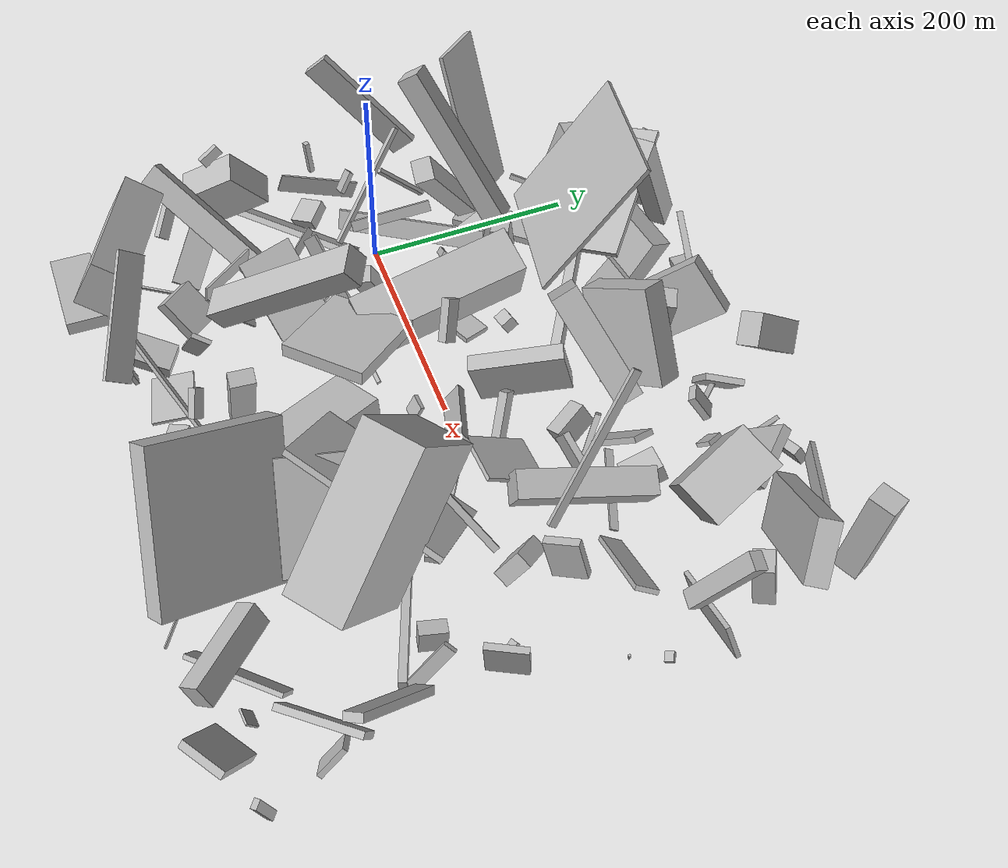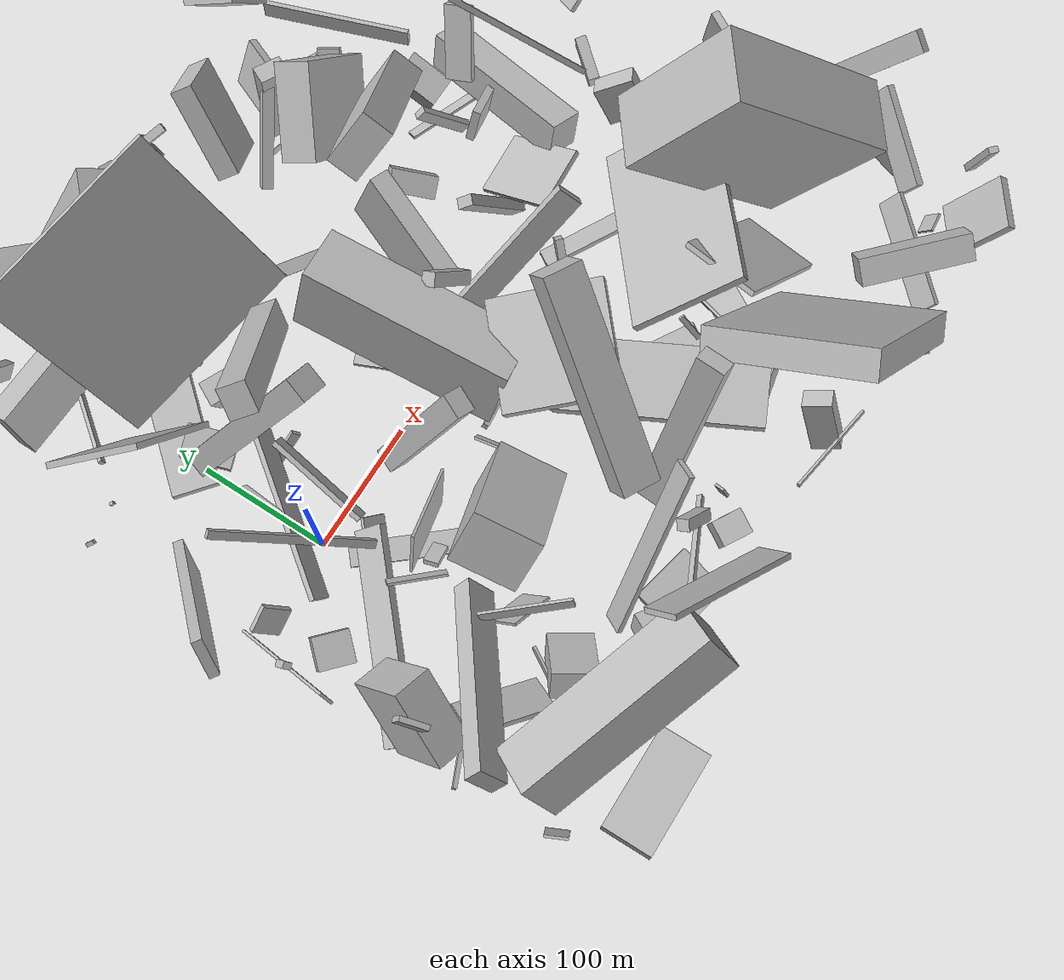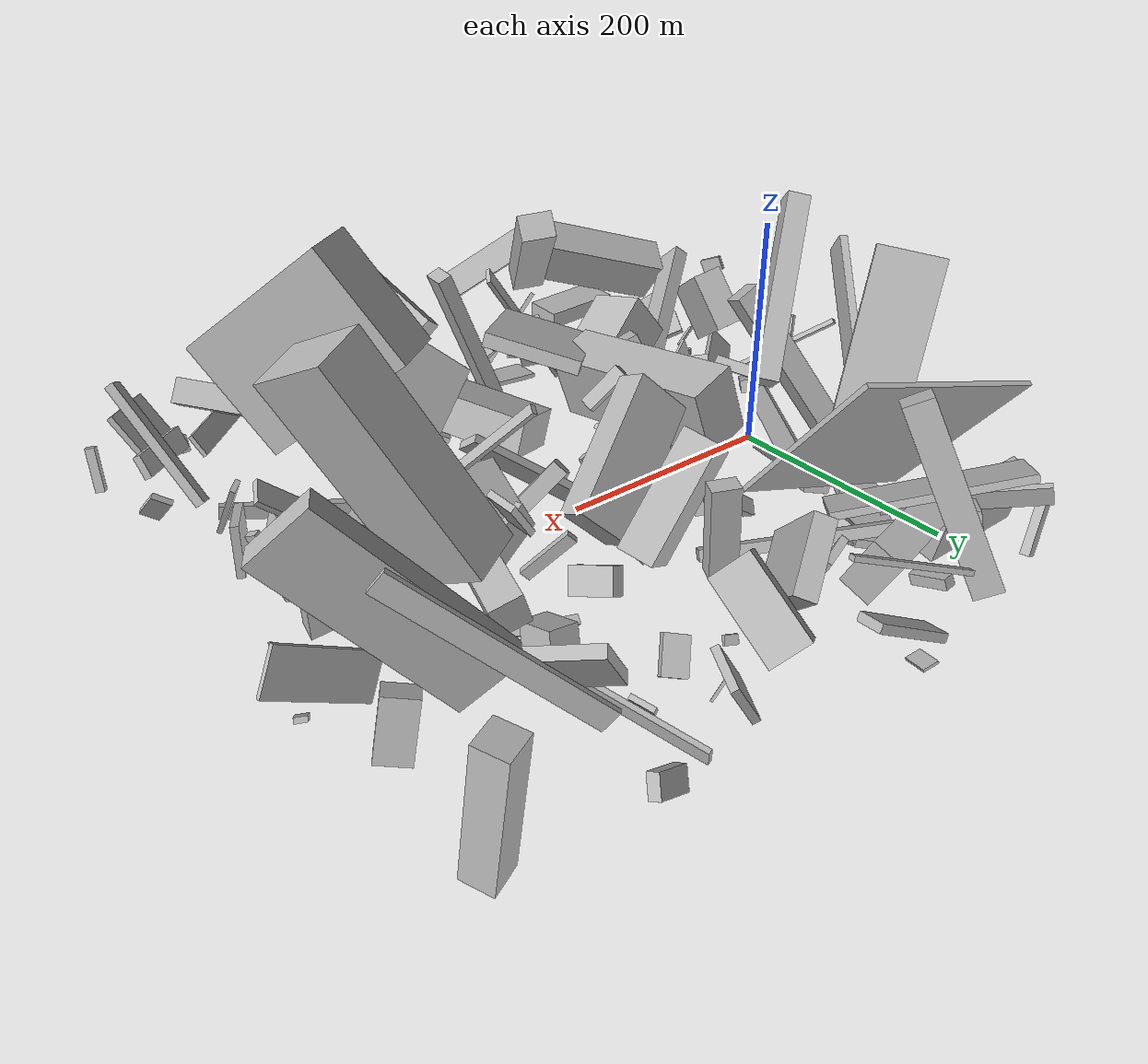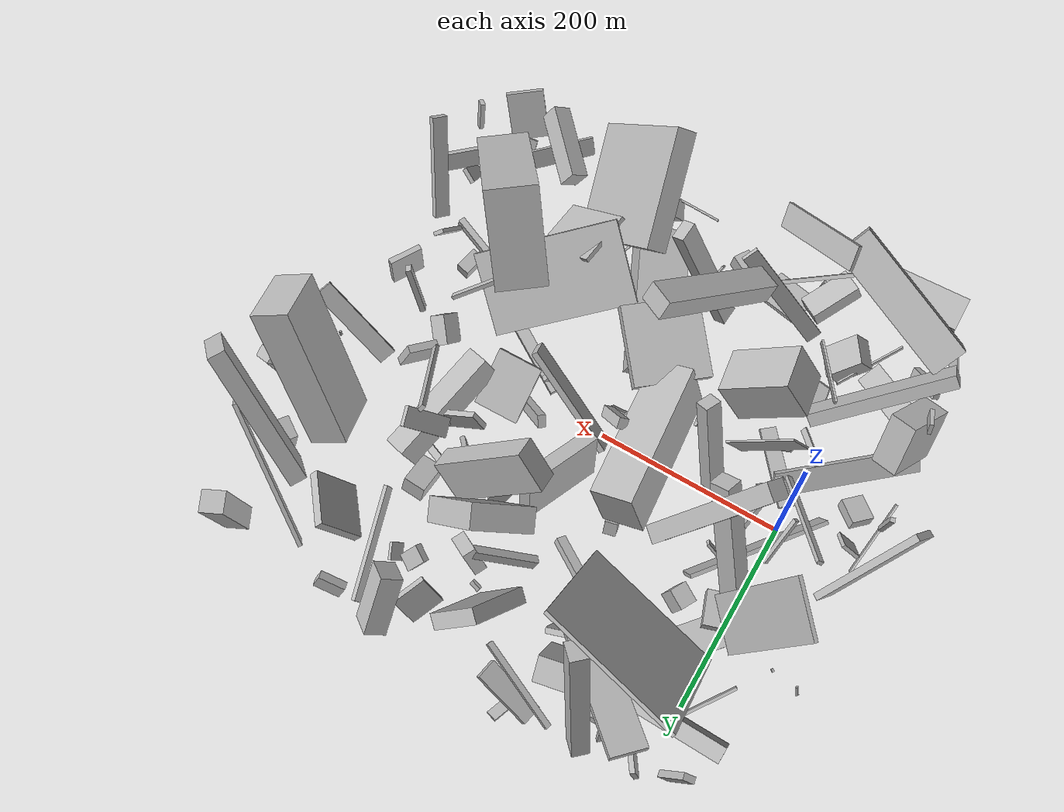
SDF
<sdf version="1.6">
 <world name="default">
  <scene>
   <sky><clouds><speed>12</speed></clouds></sky>
   <ambient>0.4 0.4 0.4 1</ambient>
   <background>0.7 0.7 0.7 1</background>
   <shadows>1</shadows>
  </scene>
  <gravity>0 0 -9.8066</gravity>
  <magnetic_field>6e-06 2.3e-05 -4.2e-05</magnetic_field>
  <physics default="0" name="default_physics" type="ode">
   <ode>
    <solver>
     <type>quick</type>
     <iters>10</iters>
     <sor>1.0</sor>
     <use_dynamic_moi_rescaling>0</use_dynamic_moi_rescaling>
    </solver>
    <constraints>
     <cfm>0</cfm>
     <erp>0.2</erp>
     <contact_max_correcting_vel>100</contact_max_correcting_vel>
     <contact_surface_layer>0.001</contact_surface_layer>
    </constraints>
   </ode>
   <max_step_size>0.004</max_step_size>
   <real_time_factor>1</real_time_factor>
   <real_time_update_rate>250</real_time_update_rate>
  </physics>
  <light name="sun" type="directional">
   <pose>0 0 10 0 0 0</pose>
   <diffuse>0.8 0.8 0.8 1</diffuse>
   <specular>0.2 0.2 0.2 1</specular>
   <attenuation>
    <range>1000</range>
    <constant>0.9</constant>
    <linear>0.01</linear>
    <quadratic>0.001</quadratic>
   </attenuation>
   <direction>-0.5 0.1 -0.9</direction>
  </light>
  <model name="building_1">
   <static>0</static>
   <pose>120.68918492601038 161.45133720720116 22.464505296555593 -1.9657326540542763 -0.10031874197089789 2.5826246045132604</pose>
   <link name="link">
    <gravity>0</gravity>
    <pose>0 0 5.0 0 0 0</pose>
    <collision name="collision"><geometry><box><size>150 9 10</size></box></geometry></collision>
    <visual name="visual">
     <cast_shadows>0</cast_shadows>
     <geometry><box><size>150 9 10</size></box></geometry>
     <material>
      <script>
       <uri>model://HANNAS_wall/materials/scripts</uri>
       <uri>model://HANNAS_wall/materials/textures</uri>
       <name>vrc/HANNAS_wall</name>
      </script>
     </material>
    </visual>
   </link>
  </model>
  <model name="building_2">
   <static>0</static>
   <pose>130.73497278025522 190.37755811783416 24.62487884282549 1.9944365662318615 -0.22942561202438608 -2.8692951318957665</pose>
   <link name="link">
    <gravity>0</gravity>
    <pose>0 0 3.0 0 0 0</pose>
    <collision name="collision"><geometry><box><size>28 42 6</size></box></geometry></collision>
    <visual name="visual">
     <cast_shadows>0</cast_shadows>
     <geometry><box><size>28 42 6</size></box></geometry>
     <material>
      <script>
       <uri>model://HANNAS_wall/materials/scripts</uri>
       <uri>model://HANNAS_wall/materials/textures</uri>
       <name>vrc/HANNAS_wall</name>
      </script>
     </material>
    </visual>
   </link>
  </model>
  <model name="building_3">
   <static>0</static>
   <pose>352.0127641518744 68.85369513316131 122.52426138870983 0.9390544121925753 -0.49572315677490775 -0.017234432638625136</pose>
   <link name="link">
    <gravity>0</gravity>
    <pose>0 0 3.5 0 0 0</pose>
    <collision name="collision"><geometry><box><size>4 143 7</size></box></geometry></collision>
    <visual name="visual">
     <cast_shadows>0</cast_shadows>
     <geometry><box><size>4 143 7</size></box></geometry>
     <material>
      <script>
       <uri>model://HANNAS_wall/materials/scripts</uri>
       <uri>model://HANNAS_wall/materials/textures</uri>
       <name>vrc/HANNAS_wall</name>
      </script>
     </material>
    </visual>
   </link>
  </model>
  <model name="building_4">
   <static>0</static>
   <pose>351.14596619945087 272.3230376288432 16.891708726268188 -2.0396949758571123 0.4229398748092815 -2.9987078818574395</pose>
   <link name="link">
    <gravity>0</gravity>
    <pose>0 0 4.5 0 0 0</pose>
    <collision name="collision"><geometry><box><size>28 16 9</size></box></geometry></collision>
    <visual name="visual">
     <cast_shadows>0</cast_shadows>
     <geometry><box><size>28 16 9</size></box></geometry>
     <material>
      <script>
       <uri>model://HANNAS_wall/materials/scripts</uri>
       <uri>model://HANNAS_wall/materials/textures</uri>
       <name>vrc/HANNAS_wall</name>
      </script>
     </material>
    </visual>
   </link>
  </model>
  <model name="building_5">
   <static>0</static>
   <pose>271.421746593213 -23.621485639629242 16.13431606164099 1.563093900149482 -0.6673275288255832 0.806832439746451</pose>
   <link name="link">
    <gravity>0</gravity>
    <pose>0 0 3.0 0 0 0</pose>
    <collision name="collision"><geometry><box><size>20 10 6</size></box></geometry></collision>
    <visual name="visual">
     <cast_shadows>0</cast_shadows>
     <geometry><box><size>20 10 6</size></box></geometry>
     <material>
      <script>
       <uri>model://HANNAS_wall/materials/scripts</uri>
       <uri>model://HANNAS_wall/materials/textures</uri>
       <name>vrc/HANNAS_wall</name>
      </script>
     </material>
    </visual>
   </link>
  </model>
  <model name="building_6">
   <static>0</static>
   <pose>92.53380347028127 89.72127168961224 117.08261155660414 0.6617011113182438 -0.2046360781055444 -0.725545873856405</pose>
   <link name="link">
    <gravity>0</gravity>
    <pose>0 0 75.0 0 0 0</pose>
    <collision name="collision"><geometry><box><size>18 21 150</size></box></geometry></collision>
    <visual name="visual">
     <cast_shadows>0</cast_shadows>
     <geometry><box><size>18 21 150</size></box></geometry>
     <material>
      <script>
       <uri>model://HANNAS_wall/materials/scripts</uri>
       <uri>model://HANNAS_wall/materials/textures</uri>
       <name>vrc/HANNAS_wall</name>
      </script>
     </material>
    </visual>
   </link>
  </model>
  <model name="building_7">
   <static>0</static>
   <pose>41.45888832227331 120.11826827299603 32.789335386937736 -1.3782574865889343 0.18848480692037026 -2.0500685810273795</pose>
   <link name="link">
    <gravity>0</gravity>
    <pose>0 0 10.5 0 0 0</pose>
    <collision name="collision"><geometry><box><size>18 28 21</size></box></geometry></collision>
    <visual name="visual">
     <cast_shadows>0</cast_shadows>
     <geometry><box><size>18 28 21</size></box></geometry>
     <material>
      <script>
       <uri>model://HANNAS_wall/materials/scripts</uri>
       <uri>model://HANNAS_wall/materials/textures</uri>
       <name>vrc/HANNAS_wall</name>
      </script>
     </material>
    </visual>
   </link>
  </model>
  <model name="building_8">
   <static>0</static>
   <pose>34.0836836755247 208.5707553289479 33.629238351588484 1.2905708604022932 0.3872400095972703 -2.054553452792674</pose>
   <link name="link">
    <gravity>0</gravity>
    <pose>0 0 17.5 0 0 0</pose>
    <collision name="collision"><geometry><box><size>11 5 35</size></box></geometry></collision>
    <visual name="visual">
     <cast_shadows>0</cast_shadows>
     <geometry><box><size>11 5 35</size></box></geometry>
     <material>
      <script>
       <uri>model://HANNAS_wall/materials/scripts</uri>
       <uri>model://HANNAS_wall/materials/textures</uri>
       <name>vrc/HANNAS_wall</name>
      </script>
     </material>
    </visual>
   </link>
  </model>
  <model name="building_9">
   <static>0</static>
   <pose>155.23234482368116 -216.74964952536408 35.22265276433423 -0.6791956581982874 0.6340952250072783 1.8277188208441097</pose>
   <link name="link">
    <gravity>0</gravity>
    <pose>0 0 13.5 0 0 0</pose>
    <collision name="collision"><geometry><box><size>10 9 27</size></box></geometry></collision>
    <visual name="visual">
     <cast_shadows>0</cast_shadows>
     <geometry><box><size>10 9 27</size></box></geometry>
     <material>
      <script>
       <uri>model://HANNAS_wall/materials/scripts</uri>
       <uri>model://HANNAS_wall/materials/textures</uri>
       <name>vrc/HANNAS_wall</name>
      </script>
     </material>
    </visual>
   </link>
  </model>
  <model name="building_10">
   <static>0</static>
   <pose>269.6916527284526 152.64854960087126 67.81588128043366 0.6026211159575662 -0.29611658093652593 -1.1497511403101692</pose>
   <link name="link">
    <gravity>0</gravity>
    <pose>0 0 43.5 0 0 0</pose>
    <collision name="collision"><geometry><box><size>25 66 87</size></box></geometry></collision>
    <visual name="visual">
     <cast_shadows>0</cast_shadows>
     <geometry><box><size>25 66 87</size></box></geometry>
     <material>
      <script>
       <uri>model://HANNAS_wall/materials/scripts</uri>
       <uri>model://HANNAS_wall/materials/textures</uri>
       <name>vrc/HANNAS_wall</name>
      </script>
     </material>
    </visual>
   </link>
  </model>
  <model name="building_11">
   <static>0</static>
   <pose>208.10366239251405 177.88101256907066 90.39304304160237 -0.62271322165962 -0.26697087066892317 2.2608271372268716</pose>
   <link name="link">
    <gravity>0</gravity>
    <pose>0 0 5.5 0 0 0</pose>
    <collision name="collision"><geometry><box><size>8 71 11</size></box></geometry></collision>
    <visual name="visual">
     <cast_shadows>0</cast_shadows>
     <geometry><box><size>8 71 11</size></box></geometry>
     <material>
      <script>
       <uri>model://HANNAS_wall/materials/scripts</uri>
       <uri>model://HANNAS_wall/materials/textures</uri>
       <name>vrc/HANNAS_wall</name>
      </script>
     </material>
    </visual>
   </link>
  </model>
  <model name="building_12">
   <static>0</static>
   <pose>-4.96735389371024 51.39790075821095 64.99824291135502 0.41725744702888623 -0.7304555457033071 0.8065749185657416</pose>
   <link name="link">
    <gravity>0</gravity>
    <pose>0 0 27.5 0 0 0</pose>
    <collision name="collision"><geometry><box><size>5 4 55</size></box></geometry></collision>
    <visual name="visual">
     <cast_shadows>0</cast_shadows>
     <geometry><box><size>5 4 55</size></box></geometry>
     <material>
      <script>
       <uri>model://HANNAS_wall/materials/scripts</uri>
       <uri>model://HANNAS_wall/materials/textures</uri>
       <name>vrc/HANNAS_wall</name>
      </script>
     </material>
    </visual>
   </link>
  </model>
  <model name="building_13">
   <static>0</static>
   <pose>346.7322080090878 -160.80504800132942 55.76217485513511 0.8082823899033313 -0.10583015550256554 -1.7351436863449097</pose>
   <link name="link">
    <gravity>0</gravity>
    <pose>0 0 48.5 0 0 0</pose>
    <collision name="collision"><geometry><box><size>57 4 97</size></box></geometry></collision>
    <visual name="visual">
     <cast_shadows>0</cast_shadows>
     <geometry><box><size>57 4 97</size></box></geometry>
     <material>
      <script>
       <uri>model://HANNAS_wall/materials/scripts</uri>
       <uri>model://HANNAS_wall/materials/textures</uri>
       <name>vrc/HANNAS_wall</name>
      </script>
     </material>
    </visual>
   </link>
  </model>
  <model name="building_14">
   <static>0</static>
   <pose>237.87747425466506 2.290979845805071 51.56819352941494 2.357849785618455 0.5709832682782415 0.7369884780921414</pose>
   <link name="link">
    <gravity>0</gravity>
    <pose>0 0 10.0 0 0 0</pose>
    <collision name="collision"><geometry><box><size>7 126 20</size></box></geometry></collision>
    <visual name="visual">
     <cast_shadows>0</cast_shadows>
     <geometry><box><size>7 126 20</size></box></geometry>
     <material>
      <script>
       <uri>model://HANNAS_wall/materials/scripts</uri>
       <uri>model://HANNAS_wall/materials/textures</uri>
       <name>vrc/HANNAS_wall</name>
      </script>
     </material>
    </visual>
   </link>
  </model>
  <model name="building_15">
   <static>0</static>
   <pose>25.864079378184435 -191.29495956231472 25.49021484575989 3.046435150158554 -0.7062382686872735 -2.496962625906016</pose>
   <link name="link">
    <gravity>0</gravity>
    <pose>0 0 11.0 0 0 0</pose>
    <collision name="collision"><geometry><box><size>42 33 22</size></box></geometry></collision>
    <visual name="visual">
     <cast_shadows>0</cast_shadows>
     <geometry><box><size>42 33 22</size></box></geometry>
     <material>
      <script>
       <uri>model://HANNAS_wall/materials/scripts</uri>
       <uri>model://HANNAS_wall/materials/textures</uri>
       <name>vrc/HANNAS_wall</name>
      </script>
     </material>
    </visual>
   </link>
  </model>
  <model name="building_16">
   <static>0</static>
   <pose>398.97003732014093 -154.1702490644935 109.54044638705864 0.029866214052484026 -0.9027827413062709 -0.9384277073334496</pose>
   <link name="link">
    <gravity>0</gravity>
    <pose>0 0 69.5 0 0 0</pose>
    <collision name="collision"><geometry><box><size>102 51 139</size></box></geometry></collision>
    <visual name="visual">
     <cast_shadows>0</cast_shadows>
     <geometry><box><size>102 51 139</size></box></geometry>
     <material>
      <script>
       <uri>model://HANNAS_wall/materials/scripts</uri>
       <uri>model://HANNAS_wall/materials/textures</uri>
       <name>vrc/HANNAS_wall</name>
      </script>
     </material>
    </visual>
   </link>
  </model>
  <model name="building_17">
   <static>0</static>
   <pose>275.35121001154914 -205.3219912383288 23.209319272910815 0.33802681908174914 -0.3035855335651364 -1.4567776951393692</pose>
   <link name="link">
    <gravity>0</gravity>
    <pose>0 0 6.5 0 0 0</pose>
    <collision name="collision"><geometry><box><size>4 68 13</size></box></geometry></collision>
    <visual name="visual">
     <cast_shadows>0</cast_shadows>
     <geometry><box><size>4 68 13</size></box></geometry>
     <material>
      <script>
       <uri>model://HANNAS_wall/materials/scripts</uri>
       <uri>model://HANNAS_wall/materials/textures</uri>
       <name>vrc/HANNAS_wall</name>
      </script>
     </material>
    </visual>
   </link>
  </model>
  <model name="building_18">
   <static>0</static>
   <pose>194.88710801433808 -154.11973293101568 35.85209927569337 0.45012844119730017 -1.310467868651778 -3.1396361202172685</pose>
   <link name="link">
    <gravity>0</gravity>
    <pose>0 0 26.0 0 0 0</pose>
    <collision name="collision"><geometry><box><size>34 150 52</size></box></geometry></collision>
    <visual name="visual">
     <cast_shadows>0</cast_shadows>
     <geometry><box><size>34 150 52</size></box></geometry>
     <material>
      <script>
       <uri>model://HANNAS_wall/materials/scripts</uri>
       <uri>model://HANNAS_wall/materials/textures</uri>
       <name>vrc/HANNAS_wall</name>
      </script>
     </material>
    </visual>
   </link>
  </model>
  <model name="building_19">
   <static>0</static>
   <pose>134.7772566717212 15.240827884145318 69.0632913056574 0.2894544298195925 -0.11280912041668863 1.6719229686661174</pose>
   <link name="link">
    <gravity>0</gravity>
    <pose>0 0 28.0 0 0 0</pose>
    <collision name="collision"><geometry><box><size>150 42 56</size></box></geometry></collision>
    <visual name="visual">
     <cast_shadows>0</cast_shadows>
     <geometry><box><size>150 42 56</size></box></geometry>
     <material>
      <script>
       <uri>model://HANNAS_wall/materials/scripts</uri>
       <uri>model://HANNAS_wall/materials/textures</uri>
       <name>vrc/HANNAS_wall</name>
      </script>
     </material>
    </visual>
   </link>
  </model>
  <model name="building_20">
   <static>0</static>
   <pose>406.2985025229419 41.731602334816884 56.30317270117865 1.9301400106152236 -0.1741453656008983 -0.7145502059853779</pose>
   <link name="link">
    <gravity>0</gravity>
    <pose>0 0 15.5 0 0 0</pose>
    <collision name="collision"><geometry><box><size>8 39 31</size></box></geometry></collision>
    <visual name="visual">
     <cast_shadows>0</cast_shadows>
     <geometry><box><size>8 39 31</size></box></geometry>
     <material>
      <script>
       <uri>model://HANNAS_wall/materials/scripts</uri>
       <uri>model://HANNAS_wall/materials/textures</uri>
       <name>vrc/HANNAS_wall</name>
      </script>
     </material>
    </visual>
   </link>
  </model>
  <model name="building_21">
   <static>0</static>
   <pose>20.494141089857177 63.231935937291645 106.6910172469888 2.083222710408784 -0.3469339662020165 1.2776833711083164</pose>
   <link name="link">
    <gravity>0</gravity>
    <pose>0 0 10.5 0 0 0</pose>
    <collision name="collision"><geometry><box><size>18 150 21</size></box></geometry></collision>
    <visual name="visual">
     <cast_shadows>0</cast_shadows>
     <geometry><box><size>18 150 21</size></box></geometry>
     <material>
      <script>
       <uri>model://HANNAS_wall/materials/scripts</uri>
       <uri>model://HANNAS_wall/materials/textures</uri>
       <name>vrc/HANNAS_wall</name>
      </script>
     </material>
    </visual>
   </link>
  </model>
  <model name="building_22">
   <static>0</static>
   <pose>66.6594670400037 182.8771307064637 98.99616147028709 0.9440336586996503 -0.1904546695611779 -0.21939582334426744</pose>
   <link name="link">
    <gravity>0</gravity>
    <pose>0 0 2.0 0 0 0</pose>
    <collision name="collision"><geometry><box><size>150 150 4</size></box></geometry></collision>
    <visual name="visual">
     <cast_shadows>0</cast_shadows>
     <geometry><box><size>150 150 4</size></box></geometry>
     <material>
      <script>
       <uri>model://HANNAS_wall/materials/scripts</uri>
       <uri>model://HANNAS_wall/materials/textures</uri>
       <name>vrc/HANNAS_wall</name>
      </script>
     </material>
    </visual>
   </link>
  </model>
  <model name="building_23">
   <static>0</static>
   <pose>122.0657754250803 182.04361859381285 62.13934422297965 -1.3091612095978662 -0.23787313093001133 0.7982923186898688</pose>
   <link name="link">
    <gravity>0</gravity>
    <pose>0 0 70.0 0 0 0</pose>
    <collision name="collision"><geometry><box><size>37 6 140</size></box></geometry></collision>
    <visual name="visual">
     <cast_shadows>0</cast_shadows>
     <geometry><box><size>37 6 140</size></box></geometry>
     <material>
      <script>
       <uri>model://HANNAS_wall/materials/scripts</uri>
       <uri>model://HANNAS_wall/materials/textures</uri>
       <name>vrc/HANNAS_wall</name>
      </script>
     </material>
    </visual>
   </link>
  </model>
  <model name="building_24">
   <static>0</static>
   <pose>58.82767965866584 -106.76726953632065 54.00887933002582 0.6369152672619559 -0.2053517548228588 1.721045755637067</pose>
   <link name="link">
    <gravity>0</gravity>
    <pose>0 0 23.5 0 0 0</pose>
    <collision name="collision"><geometry><box><size>50 77 47</size></box></geometry></collision>
    <visual name="visual">
     <cast_shadows>0</cast_shadows>
     <geometry><box><size>50 77 47</size></box></geometry>
     <material>
      <script>
       <uri>model://HANNAS_wall/materials/scripts</uri>
       <uri>model://HANNAS_wall/materials/textures</uri>
       <name>vrc/HANNAS_wall</name>
      </script>
     </material>
    </visual>
   </link>
  </model>
  <model name="building_25">
   <static>0</static>
   <pose>296.65571595458874 -218.16371816673745 100.81996352203777 2.211945389465883 -0.4392059310655683 -1.3260516322903309</pose>
   <link name="link">
    <gravity>0</gravity>
    <pose>0 0 11.0 0 0 0</pose>
    <collision name="collision"><geometry><box><size>121 138 22</size></box></geometry></collision>
    <visual name="visual">
     <cast_shadows>0</cast_shadows>
     <geometry><box><size>121 138 22</size></box></geometry>
     <material>
      <script>
       <uri>model://HANNAS_wall/materials/scripts</uri>
       <uri>model://HANNAS_wall/materials/textures</uri>
       <name>vrc/HANNAS_wall</name>
      </script>
     </material>
    </visual>
   </link>
  </model>
  <model name="building_26">
   <static>0</static>
   <pose>176.5906265317878 -175.62605746606974 85.19245224577843 1.9646793592014236 0.047211926715162805 1.5064453995964082</pose>
   <link name="link">
    <gravity>0</gravity>
    <pose>0 0 6.5 0 0 0</pose>
    <collision name="collision"><geometry><box><size>21 150 13</size></box></geometry></collision>
    <visual name="visual">
     <cast_shadows>0</cast_shadows>
     <geometry><box><size>21 150 13</size></box></geometry>
     <material>
      <script>
       <uri>model://HANNAS_wall/materials/scripts</uri>
       <uri>model://HANNAS_wall/materials/textures</uri>
       <name>vrc/HANNAS_wall</name>
      </script>
     </material>
    </visual>
   </link>
  </model>
  <model name="building_27">
   <static>0</static>
   <pose>231.81833110050755 186.4684938501138 58.32583272100922 0.053317810930111814 -0.05891769316808183 2.6690680532145854</pose>
   <link name="link">
    <gravity>0</gravity>
    <pose>0 0 34.5 0 0 0</pose>
    <collision name="collision"><geometry><box><size>20 13 69</size></box></geometry></collision>
    <visual name="visual">
     <cast_shadows>0</cast_shadows>
     <geometry><box><size>20 13 69</size></box></geometry>
     <material>
      <script>
       <uri>model://HANNAS_wall/materials/scripts</uri>
       <uri>model://HANNAS_wall/materials/textures</uri>
       <name>vrc/HANNAS_wall</name>
      </script>
     </material>
    </visual>
   </link>
  </model>
  <model name="building_28">
   <static>0</static>
   <pose>409.78417329256786 57.91215758363532 84.76116309426942 -0.4402261223009895 0.7804004660410867 -0.7560465942532574</pose>
   <link name="link">
    <gravity>0</gravity>
    <pose>0 0 46.5 0 0 0</pose>
    <collision name="collision"><geometry><box><size>4 18 93</size></box></geometry></collision>
    <visual name="visual">
     <cast_shadows>0</cast_shadows>
     <geometry><box><size>4 18 93</size></box></geometry>
     <material>
      <script>
       <uri>model://HANNAS_wall/materials/scripts</uri>
       <uri>model://HANNAS_wall/materials/textures</uri>
       <name>vrc/HANNAS_wall</name>
      </script>
     </material>
    </visual>
   </link>
  </model>
  <model name="building_29">
   <static>0</static>
   <pose>473.13118394224466 -142.75542190976944 93.24000216343464 -2.5090713097596655 -0.8754352182857953 -1.103711679919635</pose>
   <link name="link">
    <gravity>0</gravity>
    <pose>0 0 3.5 0 0 0</pose>
    <collision name="collision"><geometry><box><size>107 16 7</size></box></geometry></collision>
    <visual name="visual">
     <cast_shadows>0</cast_shadows>
     <geometry><box><size>107 16 7</size></box></geometry>
     <material>
      <script>
       <uri>model://HANNAS_wall/materials/scripts</uri>
       <uri>model://HANNAS_wall/materials/textures</uri>
       <name>vrc/HANNAS_wall</name>
      </script>
     </material>
    </visual>
   </link>
  </model>
  <model name="building_30">
   <static>0</static>
   <pose>257.9153695807103 92.15419698621969 22.5616210501819 2.607225962856432 -0.2615098005218977 2.056325890839951</pose>
   <link name="link">
    <gravity>0</gravity>
    <pose>0 0 11.0 0 0 0</pose>
    <collision name="collision"><geometry><box><size>35 17 22</size></box></geometry></collision>
    <visual name="visual">
     <cast_shadows>0</cast_shadows>
     <geometry><box><size>35 17 22</size></box></geometry>
     <material>
      <script>
       <uri>model://HANNAS_wall/materials/scripts</uri>
       <uri>model://HANNAS_wall/materials/textures</uri>
       <name>vrc/HANNAS_wall</name>
      </script>
     </material>
    </visual>
   </link>
  </model>
  <model name="building_31">
   <static>0</static>
   <pose>336.20162663925566 214.10482475108705 16.428369056676065 -0.24894715985904242 -0.10599092141484638 -1.2882932310939565</pose>
   <link name="link">
    <gravity>0</gravity>
    <pose>0 0 6.0 0 0 0</pose>
    <collision name="collision"><geometry><box><size>116 4 12</size></box></geometry></collision>
    <visual name="visual">
     <cast_shadows>0</cast_shadows>
     <geometry><box><size>116 4 12</size></box></geometry>
     <material>
      <script>
       <uri>model://HANNAS_wall/materials/scripts</uri>
       <uri>model://HANNAS_wall/materials/textures</uri>
       <name>vrc/HANNAS_wall</name>
      </script>
     </material>
    </visual>
   </link>
  </model>
  <model name="building_32">
   <static>0</static>
   <pose>334.2656831763497 100.27506406508184 101.9107099714146 2.7446630725467176 -0.848288243672968 0.5714786076773894</pose>
   <link name="link">
    <gravity>0</gravity>
    <pose>0 0 2.5 0 0 0</pose>
    <collision name="collision"><geometry><box><size>53 20 5</size></box></geometry></collision>
    <visual name="visual">
     <cast_shadows>0</cast_shadows>
     <geometry><box><size>53 20 5</size></box></geometry>
     <material>
      <script>
       <uri>model://HANNAS_wall/materials/scripts</uri>
       <uri>model://HANNAS_wall/materials/textures</uri>
       <name>vrc/HANNAS_wall</name>
      </script>
     </material>
    </visual>
   </link>
  </model>
  <model name="building_33">
   <static>0</static>
   <pose>66.62721827573576 253.70103874195712 15.122024346969797 -2.847548128330257 1.2033072120656592 1.8973044114304056</pose>
   <link name="link">
    <gravity>0</gravity>
    <pose>0 0 15.0 0 0 0</pose>
    <collision name="collision"><geometry><box><size>9 10 30</size></box></geometry></collision>
    <visual name="visual">
     <cast_shadows>0</cast_shadows>
     <geometry><box><size>9 10 30</size></box></geometry>
     <material>
      <script>
       <uri>model://HANNAS_wall/materials/scripts</uri>
       <uri>model://HANNAS_wall/materials/textures</uri>
       <name>vrc/HANNAS_wall</name>
      </script>
     </material>
    </visual>
   </link>
  </model>
  <model name="building_34">
   <static>0</static>
   <pose>-65.45230393543682 54.48668908053262 73.55328928163836 -0.03186176111053465 -0.8062408724278642 0.9922304105841109</pose>
   <link name="link">
    <gravity>0</gravity>
    <pose>0 0 59.5 0 0 0</pose>
    <collision name="collision"><geometry><box><size>29 7 119</size></box></geometry></collision>
    <visual name="visual">
     <cast_shadows>0</cast_shadows>
     <geometry><box><size>29 7 119</size></box></geometry>
     <material>
      <script>
       <uri>model://HANNAS_wall/materials/scripts</uri>
       <uri>model://HANNAS_wall/materials/textures</uri>
       <name>vrc/HANNAS_wall</name>
      </script>
     </material>
    </visual>
   </link>
  </model>
  <model name="building_35">
   <static>0</static>
   <pose>218.79266667025968 65.33158002083997 41.70170531443302 1.4018804081164236 0.23228788188039837 -1.9302767267517424</pose>
   <link name="link">
    <gravity>0</gravity>
    <pose>0 0 7.5 0 0 0</pose>
    <collision name="collision"><geometry><box><size>85 61 15</size></box></geometry></collision>
    <visual name="visual">
     <cast_shadows>0</cast_shadows>
     <geometry><box><size>85 61 15</size></box></geometry>
     <material>
      <script>
       <uri>model://HANNAS_wall/materials/scripts</uri>
       <uri>model://HANNAS_wall/materials/textures</uri>
       <name>vrc/HANNAS_wall</name>
      </script>
     </material>
    </visual>
   </link>
  </model>
  <model name="building_36">
   <static>0</static>
   <pose>-71.58749535528145 -110.97548649694622 49.82599644042703 0.31321695044260717 -0.5522279457389033 1.14321460462293</pose>
   <link name="link">
    <gravity>0</gravity>
    <pose>0 0 28.0 0 0 0</pose>
    <collision name="collision"><geometry><box><size>59 28 56</size></box></geometry></collision>
    <visual name="visual">
     <cast_shadows>0</cast_shadows>
     <geometry><box><size>59 28 56</size></box></geometry>
     <material>
      <script>
       <uri>model://HANNAS_wall/materials/scripts</uri>
       <uri>model://HANNAS_wall/materials/textures</uri>
       <name>vrc/HANNAS_wall</name>
      </script>
     </material>
    </visual>
   </link>
  </model>
  <model name="building_37">
   <static>0</static>
   <pose>10.11724520837451 32.97221965001614 34.08726024011277 2.057724107307933 0.11707482976990115 -2.2228255174994023</pose>
   <link name="link">
    <gravity>0</gravity>
    <pose>0 0 2.0 0 0 0</pose>
    <collision name="collision"><geometry><box><size>150 20 4</size></box></geometry></collision>
    <visual name="visual">
     <cast_shadows>0</cast_shadows>
     <geometry><box><size>150 20 4</size></box></geometry>
     <material>
      <script>
       <uri>model://HANNAS_wall/materials/scripts</uri>
       <uri>model://HANNAS_wall/materials/textures</uri>
       <name>vrc/HANNAS_wall</name>
      </script>
     </material>
    </visual>
   </link>
  </model>
  <model name="building_38">
   <static>0</static>
   <pose>155.93506134272093 -244.72449816559055 15.946716063355908 0.02438408609075543 -1.4110927114436425 -2.114599019833601</pose>
   <link name="link">
    <gravity>0</gravity>
    <pose>0 0 9.5 0 0 0</pose>
    <collision name="collision"><geometry><box><size>17 23 19</size></box></geometry></collision>
    <visual name="visual">
     <cast_shadows>0</cast_shadows>
     <geometry><box><size>17 23 19</size></box></geometry>
     <material>
      <script>
       <uri>model://HANNAS_wall/materials/scripts</uri>
       <uri>model://HANNAS_wall/materials/textures</uri>
       <name>vrc/HANNAS_wall</name>
      </script>
     </material>
    </visual>
   </link>
  </model>
  <model name="building_39">
   <static>0</static>
   <pose>0.6470566472135184 -248.68434530747766 86.67142131125479 0.5164116030472424 0.29255163654699873 2.8021077174908338</pose>
   <link name="link">
    <gravity>0</gravity>
    <pose>0 0 22.0 0 0 0</pose>
    <collision name="collision"><geometry><box><size>150 38 44</size></box></geometry></collision>
    <visual name="visual">
     <cast_shadows>0</cast_shadows>
     <geometry><box><size>150 38 44</size></box></geometry>
     <material>
      <script>
       <uri>model://HANNAS_wall/materials/scripts</uri>
       <uri>model://HANNAS_wall/materials/textures</uri>
       <name>vrc/HANNAS_wall</name>
      </script>
     </material>
    </visual>
   </link>
  </model>
  <model name="building_40">
   <static>0</static>
   <pose>320.0355718546526 134.17473831501744 19.12638445530611 1.4482777650327379 -0.3266651140839087 1.5735830774075494</pose>
   <link name="link">
    <gravity>0</gravity>
    <pose>0 0 11.5 0 0 0</pose>
    <collision name="collision"><geometry><box><size>34 22 23</size></box></geometry></collision>
    <visual name="visual">
     <cast_shadows>0</cast_shadows>
     <geometry><box><size>34 22 23</size></box></geometry>
     <material>
      <script>
       <uri>model://HANNAS_wall/materials/scripts</uri>
       <uri>model://HANNAS_wall/materials/textures</uri>
       <name>vrc/HANNAS_wall</name>
      </script>
     </material>
    </visual>
   </link>
  </model>
  <model name="building_41">
   <static>0</static>
   <pose>341.60662374326216 -85.14145789409254 16.170556541008395 1.436852530031555 -0.055667547855184296 1.2056905520114292</pose>
   <link name="link">
    <gravity>0</gravity>
    <pose>0 0 56.5 0 0 0</pose>
    <collision name="collision"><geometry><box><size>7 11 113</size></box></geometry></collision>
    <visual name="visual">
     <cast_shadows>0</cast_shadows>
     <geometry><box><size>7 11 113</size></box></geometry>
     <material>
      <script>
       <uri>model://HANNAS_wall/materials/scripts</uri>
       <uri>model://HANNAS_wall/materials/textures</uri>
       <name>vrc/HANNAS_wall</name>
      </script>
     </material>
    </visual>
   </link>
  </model>
  <model name="building_42">
   <static>0</static>
   <pose>-45.25352854146057 132.6801333519304 119.1791029297066 -1.1229210058751007 -1.1705584924178605 -2.8241816121307926</pose>
   <link name="link">
    <gravity>0</gravity>
    <pose>0 0 28.5 0 0 0</pose>
    <collision name="collision"><geometry><box><size>150 4 57</size></box></geometry></collision>
    <visual name="visual">
     <cast_shadows>0</cast_shadows>
     <geometry><box><size>150 4 57</size></box></geometry>
     <material>
      <script>
       <uri>model://HANNAS_wall/materials/scripts</uri>
       <uri>model://HANNAS_wall/materials/textures</uri>
       <name>vrc/HANNAS_wall</name>
      </script>
     </material>
    </visual>
   </link>
  </model>
  <model name="building_43">
   <static>0</static>
   <pose>355.4908782506045 64.87245240081512 51.61978927264356 1.2473281626751396 -0.17527101539970497 -1.7877286191008834</pose>
   <link name="link">
    <gravity>0</gravity>
    <pose>0 0 12.5 0 0 0</pose>
    <collision name="collision"><geometry><box><size>122 28 25</size></box></geometry></collision>
    <visual name="visual">
     <cast_shadows>0</cast_shadows>
     <geometry><box><size>122 28 25</size></box></geometry>
     <material>
      <script>
       <uri>model://HANNAS_wall/materials/scripts</uri>
       <uri>model://HANNAS_wall/materials/textures</uri>
       <name>vrc/HANNAS_wall</name>
      </script>
     </material>
    </visual>
   </link>
  </model>
  <model name="building_44">
   <static>0</static>
   <pose>353.7047776138186 -51.87620045410418 117.01997561058585 2.462572070406906 0.42996031222149983 -1.3111635025501447</pose>
   <link name="link">
    <gravity>0</gravity>
    <pose>0 0 2.0 0 0 0</pose>
    <collision name="collision"><geometry><box><size>6 104 4</size></box></geometry></collision>
    <visual name="visual">
     <cast_shadows>0</cast_shadows>
     <geometry><box><size>6 104 4</size></box></geometry>
     <material>
      <script>
       <uri>model://HANNAS_wall/materials/scripts</uri>
       <uri>model://HANNAS_wall/materials/textures</uri>
       <name>vrc/HANNAS_wall</name>
      </script>
     </material>
    </visual>
   </link>
  </model>
  <model name="building_45">
   <static>0</static>
   <pose>320.2121831328495 211.4679357275794 13.749399087733906 2.4448805696083675 -0.23497523686069427 -1.1495813719133037</pose>
   <link name="link">
    <gravity>0</gravity>
    <pose>0 0 7.5 0 0 0</pose>
    <collision name="collision"><geometry><box><size>18 4 15</size></box></geometry></collision>
    <visual name="visual">
     <cast_shadows>0</cast_shadows>
     <geometry><box><size>18 4 15</size></box></geometry>
     <material>
      <script>
       <uri>model://HANNAS_wall/materials/scripts</uri>
       <uri>model://HANNAS_wall/materials/textures</uri>
       <name>vrc/HANNAS_wall</name>
      </script>
     </material>
    </visual>
   </link>
  </model>
  <model name="building_46">
   <static>0</static>
   <pose>98.1031291967084 -19.045528267698394 64.49531114001341 2.035496633754219 -1.0970166542090434 -0.8408932123322227</pose>
   <link name="link">
    <gravity>0</gravity>
    <pose>0 0 9.0 0 0 0</pose>
    <collision name="collision"><geometry><box><size>113 15 18</size></box></geometry></collision>
    <visual name="visual">
     <cast_shadows>0</cast_shadows>
     <geometry><box><size>113 15 18</size></box></geometry>
     <material>
      <script>
       <uri>model://HANNAS_wall/materials/scripts</uri>
       <uri>model://HANNAS_wall/materials/textures</uri>
       <name>vrc/HANNAS_wall</name>
      </script>
     </material>
    </visual>
   </link>
  </model>
  <model name="building_47">
   <static>0</static>
   <pose>148.3384775673289 272.0799620572305 22.274149033320757 0.18369840986863778 -0.4323491475498418 -0.23836530060278613</pose>
   <link name="link">
    <gravity>0</gravity>
    <pose>0 0 3.5 0 0 0</pose>
    <collision name="collision"><geometry><box><size>64 21 7</size></box></geometry></collision>
    <visual name="visual">
     <cast_shadows>0</cast_shadows>
     <geometry><box><size>64 21 7</size></box></geometry>
     <material>
      <script>
       <uri>model://HANNAS_wall/materials/scripts</uri>
       <uri>model://HANNAS_wall/materials/textures</uri>
       <name>vrc/HANNAS_wall</name>
      </script>
     </material>
    </visual>
   </link>
  </model>
  <model name="building_48">
   <static>0</static>
   <pose>43.67775492448139 260.26501819850785 26.862530974414693 -0.21539285639404507 0.1513998096955722 -2.399931505658069</pose>
   <link name="link">
    <gravity>0</gravity>
    <pose>0 0 22.0 0 0 0</pose>
    <collision name="collision"><geometry><box><size>26 4 44</size></box></geometry></collision>
    <visual name="visual">
     <cast_shadows>0</cast_shadows>
     <geometry><box><size>26 4 44</size></box></geometry>
     <material>
      <script>
       <uri>model://HANNAS_wall/materials/scripts</uri>
       <uri>model://HANNAS_wall/materials/textures</uri>
       <name>vrc/HANNAS_wall</name>
      </script>
     </material>
    </visual>
   </link>
  </model>
  <model name="building_49">
   <static>0</static>
   <pose>28.048853276304538 10.10852847265361 74.39527984019898 -0.2091593645872243 0.5784950283849167 2.879030681604883</pose>
   <link name="link">
    <gravity>0</gravity>
    <pose>0 0 5.0 0 0 0</pose>
    <collision name="collision"><geometry><box><size>4 76 10</size></box></geometry></collision>
    <visual name="visual">
     <cast_shadows>0</cast_shadows>
     <geometry><box><size>4 76 10</size></box></geometry>
     <material>
      <script>
       <uri>model://HANNAS_wall/materials/scripts</uri>
       <uri>model://HANNAS_wall/materials/textures</uri>
       <name>vrc/HANNAS_wall</name>
      </script>
     </material>
    </visual>
   </link>
  </model>
  <model name="building_50">
   <static>0</static>
   <pose>-76.67155132828033 -133.75679055776348 109.20010032814247 1.4519032992765066 -1.1624077690116237 -1.1415930687145222</pose>
   <link name="link">
    <gravity>0</gravity>
    <pose>0 0 2.0 0 0 0</pose>
    <collision name="collision"><geometry><box><size>13 21 4</size></box></geometry></collision>
    <visual name="visual">
     <cast_shadows>0</cast_shadows>
     <geometry><box><size>13 21 4</size></box></geometry>
     <material>
      <script>
       <uri>model://HANNAS_wall/materials/scripts</uri>
       <uri>model://HANNAS_wall/materials/textures</uri>
       <name>vrc/HANNAS_wall</name>
      </script>
     </material>
    </visual>
   </link>
  </model>
  <model name="building_51">
   <static>0</static>
   <pose>447.143308683971 -267.6027939846478 42.227691159410455 3.040567215498969 -0.9457880873833623 -0.8682007279941073</pose>
   <link name="link">
    <gravity>0</gravity>
    <pose>0 0 3.5 0 0 0</pose>
    <collision name="collision"><geometry><box><size>52 40 7</size></box></geometry></collision>
    <visual name="visual">
     <cast_shadows>0</cast_shadows>
     <geometry><box><size>52 40 7</size></box></geometry>
     <material>
      <script>
       <uri>model://HANNAS_wall/materials/scripts</uri>
       <uri>model://HANNAS_wall/materials/textures</uri>
       <name>vrc/HANNAS_wall</name>
      </script>
     </material>
    </visual>
   </link>
  </model>
  <model name="building_52">
   <static>0</static>
   <pose>-15.062791142078908 1.1153730630166763 82.48051068723673 2.305550357722177 -0.7330074066793177 -1.8453470527176214</pose>
   <link name="link">
    <gravity>0</gravity>
    <pose>0 0 3.0 0 0 0</pose>
    <collision name="collision"><geometry><box><size>4 122 6</size></box></geometry></collision>
    <visual name="visual">
     <cast_shadows>0</cast_shadows>
     <geometry><box><size>4 122 6</size></box></geometry>
     <material>
      <script>
       <uri>model://HANNAS_wall/materials/scripts</uri>
       <uri>model://HANNAS_wall/materials/textures</uri>
       <name>vrc/HANNAS_wall</name>
      </script>
     </material>
    </visual>
   </link>
  </model>
  <model name="building_53">
   <static>0</static>
   <pose>-33.84201247879642 -149.3581627895657 64.3056996064691 0.6303856770719305 -0.7239598125798495 1.7625775911477737</pose>
   <link name="link">
    <gravity>0</gravity>
    <pose>0 0 7.0 0 0 0</pose>
    <collision name="collision"><geometry><box><size>24 150 14</size></box></geometry></collision>
    <visual name="visual">
     <cast_shadows>0</cast_shadows>
     <geometry><box><size>24 150 14</size></box></geometry>
     <material>
      <script>
       <uri>model://HANNAS_wall/materials/scripts</uri>
       <uri>model://HANNAS_wall/materials/textures</uri>
       <name>vrc/HANNAS_wall</name>
      </script>
     </material>
    </visual>
   </link>
  </model>
  <model name="building_54">
   <static>0</static>
   <pose>299.1345686601552 42.94752845976 39.50940518472878 0.16533238484044963 1.0051140749707599 -1.3929208963406012</pose>
   <link name="link">
    <gravity>0</gravity>
    <pose>0 0 30.5 0 0 0</pose>
    <collision name="collision"><geometry><box><size>4 47 61</size></box></geometry></collision>
    <visual name="visual">
     <cast_shadows>0</cast_shadows>
     <geometry><box><size>4 47 61</size></box></geometry>
     <material>
      <script>
       <uri>model://HANNAS_wall/materials/scripts</uri>
       <uri>model://HANNAS_wall/materials/textures</uri>
       <name>vrc/HANNAS_wall</name>
      </script>
     </material>
    </visual>
   </link>
  </model>
  <model name="building_55">
   <static>0</static>
   <pose>108.35342008683637 -192.29144181079405 66.73396188925861 1.1196604996998218 0.4348265121435806 -0.7484699216123905</pose>
   <link name="link">
    <gravity>0</gravity>
    <pose>0 0 8.5 0 0 0</pose>
    <collision name="collision"><geometry><box><size>4 150 17</size></box></geometry></collision>
    <visual name="visual">
     <cast_shadows>0</cast_shadows>
     <geometry><box><size>4 150 17</size></box></geometry>
     <material>
      <script>
       <uri>model://HANNAS_wall/materials/scripts</uri>
       <uri>model://HANNAS_wall/materials/textures</uri>
       <name>vrc/HANNAS_wall</name>
      </script>
     </material>
    </visual>
   </link>
  </model>
  <model name="building_56">
   <static>0</static>
   <pose>448.9970439224969 116.94305210319777 38.42751929280119 1.06974655189705 -0.22942385509557253 1.6201673655518098</pose>
   <link name="link">
    <gravity>0</gravity>
    <pose>0 0 37.0 0 0 0</pose>
    <collision name="collision"><geometry><box><size>4 32 74</size></box></geometry></collision>
    <visual name="visual">
     <cast_shadows>0</cast_shadows>
     <geometry><box><size>4 32 74</size></box></geometry>
     <material>
      <script>
       <uri>model://HANNAS_wall/materials/scripts</uri>
       <uri>model://HANNAS_wall/materials/textures</uri>
       <name>vrc/HANNAS_wall</name>
      </script>
     </material>
    </visual>
   </link>
  </model>
  <model name="building_57">
   <static>0</static>
   <pose>356.4395652561491 228.08573730655962 73.43851636808617 1.8143394906197459 0.5834662746108749 0.8551941055493584</pose>
   <link name="link">
    <gravity>0</gravity>
    <pose>0 0 28.5 0 0 0</pose>
    <collision name="collision"><geometry><box><size>9 51 57</size></box></geometry></collision>
    <visual name="visual">
     <cast_shadows>0</cast_shadows>
     <geometry><box><size>9 51 57</size></box></geometry>
     <material>
      <script>
       <uri>model://HANNAS_wall/materials/scripts</uri>
       <uri>model://HANNAS_wall/materials/textures</uri>
       <name>vrc/HANNAS_wall</name>
      </script>
     </material>
    </visual>
   </link>
  </model>
  <model name="building_58">
   <static>0</static>
   <pose>260.5584905077376 24.488459455909368 51.70489122324854 1.2383397169335102 -0.8414184910730053 2.5611236991652047</pose>
   <link name="link">
    <gravity>0</gravity>
    <pose>0 0 4.0 0 0 0</pose>
    <collision name="collision"><geometry><box><size>61 13 8</size></box></geometry></collision>
    <visual name="visual">
     <cast_shadows>0</cast_shadows>
     <geometry><box><size>61 13 8</size></box></geometry>
     <material>
      <script>
       <uri>model://HANNAS_wall/materials/scripts</uri>
       <uri>model://HANNAS_wall/materials/textures</uri>
       <name>vrc/HANNAS_wall</name>
      </script>
     </material>
    </visual>
   </link>
  </model>
  <model name="building_59">
   <static>0</static>
   <pose>383.71833566183125 254.5633019491852 67.60112040060852 0.9050835403720302 0.005669533655554093 0.9306886506298212</pose>
   <link name="link">
    <gravity>0</gravity>
    <pose>0 0 75.0 0 0 0</pose>
    <collision name="collision"><geometry><box><size>4 16 150</size></box></geometry></collision>
    <visual name="visual">
     <cast_shadows>0</cast_shadows>
     <geometry><box><size>4 16 150</size></box></geometry>
     <material>
      <script>
       <uri>model://HANNAS_wall/materials/scripts</uri>
       <uri>model://HANNAS_wall/materials/textures</uri>
       <name>vrc/HANNAS_wall</name>
      </script>
     </material>
    </visual>
   </link>
  </model>
  <model name="building_60">
   <static>0</static>
   <pose>488.32052491099927 88.72163590904158 5.930508036298704 -2.9617902483447334 1.0576549709236507 1.2003187688799644</pose>
   <link name="link">
    <gravity>0</gravity>
    <pose>0 0 4.0 0 0 0</pose>
    <collision name="collision"><geometry><box><size>4 9 8</size></box></geometry></collision>
    <visual name="visual">
     <cast_shadows>0</cast_shadows>
     <geometry><box><size>4 9 8</size></box></geometry>
     <material>
      <script>
       <uri>model://HANNAS_wall/materials/scripts</uri>
       <uri>model://HANNAS_wall/materials/textures</uri>
       <name>vrc/HANNAS_wall</name>
      </script>
     </material>
    </visual>
   </link>
  </model>
  <model name="building_61">
   <static>0</static>
   <pose>460.49595077800336 272.08874839928785 62.16063756286397 -0.17682511024077852 -1.4673658674885217 2.18941720285874</pose>
   <link name="link">
    <gravity>0</gravity>
    <pose>0 0 11.0 0 0 0</pose>
    <collision name="collision"><geometry><box><size>93 23 22</size></box></geometry></collision>
    <visual name="visual">
     <cast_shadows>0</cast_shadows>
     <geometry><box><size>93 23 22</size></box></geometry>
     <material>
      <script>
       <uri>model://HANNAS_wall/materials/scripts</uri>
       <uri>model://HANNAS_wall/materials/textures</uri>
       <name>vrc/HANNAS_wall</name>
      </script>
     </material>
    </visual>
   </link>
  </model>
  <model name="building_62">
   <static>0</static>
   <pose>21.955251698501662 -29.29971301496933 39.85138276120513 1.6732388194020584 -0.7305639726529239 -0.919596440189512</pose>
   <link name="link">
    <gravity>0</gravity>
    <pose>0 0 75.0 0 0 0</pose>
    <collision name="collision"><geometry><box><size>25 6 150</size></box></geometry></collision>
    <visual name="visual">
     <cast_shadows>0</cast_shadows>
     <geometry><box><size>25 6 150</size></box></geometry>
     <material>
      <script>
       <uri>model://HANNAS_wall/materials/scripts</uri>
       <uri>model://HANNAS_wall/materials/textures</uri>
       <name>vrc/HANNAS_wall</name>
      </script>
     </material>
    </visual>
   </link>
  </model>
  <model name="building_63">
   <static>0</static>
   <pose>88.70231832712545 258.0517712097698 91.98305419709573 1.823778059073785 -1.1127874750434064 -1.0537264671055462</pose>
   <link name="link">
    <gravity>0</gravity>
    <pose>0 0 9.0 0 0 0</pose>
    <collision name="collision"><geometry><box><size>150 22 18</size></box></geometry></collision>
    <visual name="visual">
     <cast_shadows>0</cast_shadows>
     <geometry><box><size>150 22 18</size></box></geometry>
     <material>
      <script>
       <uri>model://HANNAS_wall/materials/scripts</uri>
       <uri>model://HANNAS_wall/materials/textures</uri>
       <name>vrc/HANNAS_wall</name>
      </script>
     </material>
    </visual>
   </link>
  </model>
  <model name="building_64">
   <static>0</static>
   <pose>422.88478441105735 199.50828231587977 80.83654382536392 0.7493625902195143 0.06405323321960309 1.0377611483007807</pose>
   <link name="link">
    <gravity>0</gravity>
    <pose>0 0 74.0 0 0 0</pose>
    <collision name="collision"><geometry><box><size>17 48 148</size></box></geometry></collision>
    <visual name="visual">
     <cast_shadows>0</cast_shadows>
     <geometry><box><size>17 48 148</size></box></geometry>
     <material>
      <script>
       <uri>model://HANNAS_wall/materials/scripts</uri>
       <uri>model://HANNAS_wall/materials/textures</uri>
       <name>vrc/HANNAS_wall</name>
      </script>
     </material>
    </visual>
   </link>
  </model>
  <model name="building_65">
   <static>0</static>
   <pose>386.3809083712303 -14.618123899439466 37.28490891264739 -0.39476335607542407 -0.4570844689023002 -0.9202858906484338</pose>
   <link name="link">
    <gravity>0</gravity>
    <pose>0 0 16.0 0 0 0</pose>
    <collision name="collision"><geometry><box><size>30 15 32</size></box></geometry></collision>
    <visual name="visual">
     <cast_shadows>0</cast_shadows>
     <geometry><box><size>30 15 32</size></box></geometry>
     <material>
      <script>
       <uri>model://HANNAS_wall/materials/scripts</uri>
       <uri>model://HANNAS_wall/materials/textures</uri>
       <name>vrc/HANNAS_wall</name>
      </script>
     </material>
    </visual>
   </link>
  </model>
  <model name="building_66">
   <static>0</static>
   <pose>10.542347712413092 153.99364912853324 8.910746619338738 1.4678345467816456 -0.010830840417592788 0.8617411571662466</pose>
   <link name="link">
    <gravity>0</gravity>
    <pose>0 0 17.0 0 0 0</pose>
    <collision name="collision"><geometry><box><size>126 7 34</size></box></geometry></collision>
    <visual name="visual">
     <cast_shadows>0</cast_shadows>
     <geometry><box><size>126 7 34</size></box></geometry>
     <material>
      <script>
       <uri>model://HANNAS_wall/materials/scripts</uri>
       <uri>model://HANNAS_wall/materials/textures</uri>
       <name>vrc/HANNAS_wall</name>
      </script>
     </material>
    </visual>
   </link>
  </model>
  <model name="building_67">
   <static>0</static>
   <pose>136.2206496573705 43.83406878992356 31.63077013633476 -3.0366959140460628 -0.1353542403393924 -1.2035042244865528</pose>
   <link name="link">
    <gravity>0</gravity>
    <pose>0 0 2.5 0 0 0</pose>
    <collision name="collision"><geometry><box><size>26 32 5</size></box></geometry></collision>
    <visual name="visual">
     <cast_shadows>0</cast_shadows>
     <geometry><box><size>26 32 5</size></box></geometry>
     <material>
      <script>
       <uri>model://HANNAS_wall/materials/scripts</uri>
       <uri>model://HANNAS_wall/materials/textures</uri>
       <name>vrc/HANNAS_wall</name>
      </script>
     </material>
    </visual>
   </link>
  </model>
  <model name="building_68">
   <static>0</static>
   <pose>135.87816562739158 261.97850091111667 65.56254263883918 -1.273145413763801 -0.2924696258033734 -0.4130796004737364</pose>
   <link name="link">
    <gravity>0</gravity>
    <pose>0 0 3.0 0 0 0</pose>
    <collision name="collision"><geometry><box><size>94 4 6</size></box></geometry></collision>
    <visual name="visual">
     <cast_shadows>0</cast_shadows>
     <geometry><box><size>94 4 6</size></box></geometry>
     <material>
      <script>
       <uri>model://HANNAS_wall/materials/scripts</uri>
       <uri>model://HANNAS_wall/materials/textures</uri>
       <name>vrc/HANNAS_wall</name>
      </script>
     </material>
    </visual>
   </link>
  </model>
  <model name="building_69">
   <static>0</static>
   <pose>281.32636424148245 -68.94042906636898 71.01725559378316 -0.9707989765833269 -0.23460316225815703 -2.477251918317001</pose>
   <link name="link">
    <gravity>0</gravity>
    <pose>0 0 42.5 0 0 0</pose>
    <collision name="collision"><geometry><box><size>147 6 85</size></box></geometry></collision>
    <visual name="visual">
     <cast_shadows>0</cast_shadows>
     <geometry><box><size>147 6 85</size></box></geometry>
     <material>
      <script>
       <uri>model://HANNAS_wall/materials/scripts</uri>
       <uri>model://HANNAS_wall/materials/textures</uri>
       <name>vrc/HANNAS_wall</name>
      </script>
     </material>
    </visual>
   </link>
  </model>
  <model name="building_70">
   <static>0</static>
   <pose>401.97318024882236 143.94262509601515 116.84963937059754 0.46283116043441863 0.2774796920781997 0.42658962389295285</pose>
   <link name="link">
    <gravity>0</gravity>
    <pose>0 0 75.0 0 0 0</pose>
    <collision name="collision"><geometry><box><size>36 57 150</size></box></geometry></collision>
    <visual name="visual">
     <cast_shadows>0</cast_shadows>
     <geometry><box><size>36 57 150</size></box></geometry>
     <material>
      <script>
       <uri>model://HANNAS_wall/materials/scripts</uri>
       <uri>model://HANNAS_wall/materials/textures</uri>
       <name>vrc/HANNAS_wall</name>
      </script>
     </material>
    </visual>
   </link>
  </model>
  <model name="building_71">
   <static>0</static>
   <pose>120.81248987893424 -173.1858720522274 130.9942589316468 -0.2032277389310323 -0.9439560517571628 -1.8860181093547188</pose>
   <link name="link">
    <gravity>0</gravity>
    <pose>0 0 75.0 0 0 0</pose>
    <collision name="collision"><geometry><box><size>21 27 150</size></box></geometry></collision>
    <visual name="visual">
     <cast_shadows>0</cast_shadows>
     <geometry><box><size>21 27 150</size></box></geometry>
     <material>
      <script>
       <uri>model://HANNAS_wall/materials/scripts</uri>
       <uri>model://HANNAS_wall/materials/textures</uri>
       <name>vrc/HANNAS_wall</name>
      </script>
     </material>
    </visual>
   </link>
  </model>
  <model name="building_72">
   <static>0</static>
   <pose>19.413442538945542 87.12878610867142 11.709614290428373 0.596584569083681 -1.3763904979390882 -1.8360597934005218</pose>
   <link name="link">
    <gravity>0</gravity>
    <pose>0 0 18.5 0 0 0</pose>
    <collision name="collision"><geometry><box><size>11 25 37</size></box></geometry></collision>
    <visual name="visual">
     <cast_shadows>0</cast_shadows>
     <geometry><box><size>11 25 37</size></box></geometry>
     <material>
      <script>
       <uri>model://HANNAS_wall/materials/scripts</uri>
       <uri>model://HANNAS_wall/materials/textures</uri>
       <name>vrc/HANNAS_wall</name>
      </script>
     </material>
    </visual>
   </link>
  </model>
  <model name="building_73">
   <static>0</static>
   <pose>479.32337742362046 -193.72569129652214 17.79218168637988 2.203436998945835 -0.513512652577913 -2.341326796653107</pose>
   <link name="link">
    <gravity>0</gravity>
    <pose>0 0 8.5 0 0 0</pose>
    <collision name="collision"><geometry><box><size>5 34 17</size></box></geometry></collision>
    <visual name="visual">
     <cast_shadows>0</cast_shadows>
     <geometry><box><size>5 34 17</size></box></geometry>
     <material>
      <script>
       <uri>model://HANNAS_wall/materials/scripts</uri>
       <uri>model://HANNAS_wall/materials/textures</uri>
       <name>vrc/HANNAS_wall</name>
      </script>
     </material>
    </visual>
   </link>
  </model>
  <model name="building_74">
   <static>0</static>
   <pose>-26.410802282215954 -160.65702881271403 29.20511937772388 0.8206826460790959 -0.9667604366058886 0.20455205610360064</pose>
   <link name="link">
    <gravity>0</gravity>
    <pose>0 0 13.5 0 0 0</pose>
    <collision name="collision"><geometry><box><size>5 67 27</size></box></geometry></collision>
    <visual name="visual">
     <cast_shadows>0</cast_shadows>
     <geometry><box><size>5 67 27</size></box></geometry>
     <material>
      <script>
       <uri>model://HANNAS_wall/materials/scripts</uri>
       <uri>model://HANNAS_wall/materials/textures</uri>
       <name>vrc/HANNAS_wall</name>
      </script>
     </material>
    </visual>
   </link>
  </model>
  <model name="building_75">
   <static>0</static>
   <pose>319.93343101563505 68.36196335973912 59.8913492377411 1.476491888612136 -0.47175757138286717 -2.894179934149343</pose>
   <link name="link">
    <gravity>0</gravity>
    <pose>0 0 3.0 0 0 0</pose>
    <collision name="collision"><geometry><box><size>44 24 6</size></box></geometry></collision>
    <visual name="visual">
     <cast_shadows>0</cast_shadows>
     <geometry><box><size>44 24 6</size></box></geometry>
     <material>
      <script>
       <uri>model://HANNAS_wall/materials/scripts</uri>
       <uri>model://HANNAS_wall/materials/textures</uri>
       <name>vrc/HANNAS_wall</name>
      </script>
     </material>
    </visual>
   </link>
  </model>
  <model name="building_76">
   <static>0</static>
   <pose>143.78392744442283 -52.205304445585064 10.988437874693037 0.7868912275178591 1.156255421118373 2.455073361720852</pose>
   <link name="link">
    <gravity>0</gravity>
    <pose>0 0 2.0 0 0 0</pose>
    <collision name="collision"><geometry><box><size>5 26 4</size></box></geometry></collision>
    <visual name="visual">
     <cast_shadows>0</cast_shadows>
     <geometry><box><size>5 26 4</size></box></geometry>
     <material>
      <script>
       <uri>model://HANNAS_wall/materials/scripts</uri>
       <uri>model://HANNAS_wall/materials/textures</uri>
       <name>vrc/HANNAS_wall</name>
      </script>
     </material>
    </visual>
   </link>
  </model>
  <model name="building_77">
   <static>0</static>
   <pose>461.42619113647646 -45.35329713407715 33.58959965957743 -0.07816284151549588 -0.005811306669042181 2.646631163815487</pose>
   <link name="link">
    <gravity>0</gravity>
    <pose>0 0 20.0 0 0 0</pose>
    <collision name="collision"><geometry><box><size>6 35 40</size></box></geometry></collision>
    <visual name="visual">
     <cast_shadows>0</cast_shadows>
     <geometry><box><size>6 35 40</size></box></geometry>
     <material>
      <script>
       <uri>model://HANNAS_wall/materials/scripts</uri>
       <uri>model://HANNAS_wall/materials/textures</uri>
       <name>vrc/HANNAS_wall</name>
      </script>
     </material>
    </visual>
   </link>
  </model>
  <model name="building_78">
   <static>0</static>
   <pose>62.22215322579418 162.05701319750713 17.90239504501308 2.9242109946883885 -0.5816669581069527 0.039926443531390375</pose>
   <link name="link">
    <gravity>0</gravity>
    <pose>0 0 7.5 0 0 0</pose>
    <collision name="collision"><geometry><box><size>19 20 15</size></box></geometry></collision>
    <visual name="visual">
     <cast_shadows>0</cast_shadows>
     <geometry><box><size>19 20 15</size></box></geometry>
     <material>
      <script>
       <uri>model://HANNAS_wall/materials/scripts</uri>
       <uri>model://HANNAS_wall/materials/textures</uri>
       <name>vrc/HANNAS_wall</name>
      </script>
     </material>
    </visual>
   </link>
  </model>
  <model name="building_79">
   <static>0</static>
   <pose>61.01669095939353 -244.2957438950404 19.696736795242913 -0.20308086038258255 -0.272240307829673 -2.11437407895956</pose>
   <link name="link">
    <gravity>0</gravity>
    <pose>0 0 9.5 0 0 0</pose>
    <collision name="collision"><geometry><box><size>54 26 19</size></box></geometry></collision>
    <visual name="visual">
     <cast_shadows>0</cast_shadows>
     <geometry><box><size>54 26 19</size></box></geometry>
     <material>
      <script>
       <uri>model://HANNAS_wall/materials/scripts</uri>
       <uri>model://HANNAS_wall/materials/textures</uri>
       <name>vrc/HANNAS_wall</name>
      </script>
     </material>
    </visual>
   </link>
  </model>
  <model name="building_80">
   <static>0</static>
   <pose>398.1633472714932 -242.47676080520537 39.64432349529938 0.9921462521837967 0.06519437478967766 -2.319186184960368</pose>
   <link name="link">
    <gravity>0</gravity>
    <pose>0 0 2.0 0 0 0</pose>
    <collision name="collision"><geometry><box><size>86 20 4</size></box></geometry></collision>
    <visual name="visual">
     <cast_shadows>0</cast_shadows>
     <geometry><box><size>86 20 4</size></box></geometry>
     <material>
      <script>
       <uri>model://HANNAS_wall/materials/scripts</uri>
       <uri>model://HANNAS_wall/materials/textures</uri>
       <name>vrc/HANNAS_wall</name>
      </script>
     </material>
    </visual>
   </link>
  </model>
  <model name="building_81">
   <static>0</static>
   <pose>252.93475788468422 101.85983205579939 111.77847796243373 1.0320816605816145 -0.6527040098764662 -2.745251825642356</pose>
   <link name="link">
    <gravity>0</gravity>
    <pose>0 0 12.0 0 0 0</pose>
    <collision name="collision"><geometry><box><size>105 44 24</size></box></geometry></collision>
    <visual name="visual">
     <cast_shadows>0</cast_shadows>
     <geometry><box><size>105 44 24</size></box></geometry>
     <material>
      <script>
       <uri>model://HANNAS_wall/materials/scripts</uri>
       <uri>model://HANNAS_wall/materials/textures</uri>
       <name>vrc/HANNAS_wall</name>
      </script>
     </material>
    </visual>
   </link>
  </model>
  <model name="building_82">
   <static>0</static>
   <pose>346.82952422362763 -66.1234297804462 16.821422633426053 -1.6912155654559689 -0.009511388242024306 1.0323392576782144</pose>
   <link name="link">
    <gravity>0</gravity>
    <pose>0 0 48.0 0 0 0</pose>
    <collision name="collision"><geometry><box><size>13 7 96</size></box></geometry></collision>
    <visual name="visual">
     <cast_shadows>0</cast_shadows>
     <geometry><box><size>13 7 96</size></box></geometry>
     <material>
      <script>
       <uri>model://HANNAS_wall/materials/scripts</uri>
       <uri>model://HANNAS_wall/materials/textures</uri>
       <name>vrc/HANNAS_wall</name>
      </script>
     </material>
    </visual>
   </link>
  </model>
  <model name="building_83">
   <static>0</static>
   <pose>71.27619629044 190.2513767623026 49.976421236520935 1.3065406720978325 -0.2262993217320427 -2.46955018700079</pose>
   <link name="link">
    <gravity>0</gravity>
    <pose>0 0 58.5 0 0 0</pose>
    <collision name="collision"><geometry><box><size>5 16 117</size></box></geometry></collision>
    <visual name="visual">
     <cast_shadows>0</cast_shadows>
     <geometry><box><size>5 16 117</size></box></geometry>
     <material>
      <script>
       <uri>model://HANNAS_wall/materials/scripts</uri>
       <uri>model://HANNAS_wall/materials/textures</uri>
       <name>vrc/HANNAS_wall</name>
      </script>
     </material>
    </visual>
   </link>
  </model>
  <model name="building_84">
   <static>0</static>
   <pose>313.1314107694766 82.27680254437425 33.1340581648765 0.1239516534438897 0.7545026401138775 2.545575684948299</pose>
   <link name="link">
    <gravity>0</gravity>
    <pose>0 0 23.5 0 0 0</pose>
    <collision name="collision"><geometry><box><size>9 5 47</size></box></geometry></collision>
    <visual name="visual">
     <cast_shadows>0</cast_shadows>
     <geometry><box><size>9 5 47</size></box></geometry>
     <material>
      <script>
       <uri>model://HANNAS_wall/materials/scripts</uri>
       <uri>model://HANNAS_wall/materials/textures</uri>
       <name>vrc/HANNAS_wall</name>
      </script>
     </material>
    </visual>
   </link>
  </model>
  <model name="building_85">
   <static>0</static>
   <pose>494.4160421617978 -247.60699021692574 29.507409671976642 1.6962594632633987 -0.17174291934649885 0.8698641101099696</pose>
   <link name="link">
    <gravity>0</gravity>
    <pose>0 0 4.0 0 0 0</pose>
    <collision name="collision"><geometry><box><size>5 38 8</size></box></geometry></collision>
    <visual name="visual">
     <cast_shadows>0</cast_shadows>
     <geometry><box><size>5 38 8</size></box></geometry>
     <material>
      <script>
       <uri>model://HANNAS_wall/materials/scripts</uri>
       <uri>model://HANNAS_wall/materials/textures</uri>
       <name>vrc/HANNAS_wall</name>
      </script>
     </material>
    </visual>
   </link>
  </model>
  <model name="building_86">
   <static>0</static>
   <pose>112.2476208059426 -231.22222597365703 37.84751664972332 2.571945753365977 -0.5631387815097111 -0.8482723437944749</pose>
   <link name="link">
    <gravity>0</gravity>
    <pose>0 0 2.0 0 0 0</pose>
    <collision name="collision"><geometry><box><size>4 150 4</size></box></geometry></collision>
    <visual name="visual">
     <cast_shadows>0</cast_shadows>
     <geometry><box><size>4 150 4</size></box></geometry>
     <material>
      <script>
       <uri>model://HANNAS_wall/materials/scripts</uri>
       <uri>model://HANNAS_wall/materials/textures</uri>
       <name>vrc/HANNAS_wall</name>
      </script>
     </material>
    </visual>
   </link>
  </model>
  <model name="building_87">
   <static>0</static>
   <pose>-62.545802751245816 -15.736426754943594 34.98618311265176 0.6850251690528764 -0.5475683828368358 -1.9643627257309482</pose>
   <link name="link">
    <gravity>0</gravity>
    <pose>0 0 11.0 0 0 0</pose>
    <collision name="collision"><geometry><box><size>4 21 22</size></box></geometry></collision>
    <visual name="visual">
     <cast_shadows>0</cast_shadows>
     <geometry><box><size>4 21 22</size></box></geometry>
     <material>
      <script>
       <uri>model://HANNAS_wall/materials/scripts</uri>
       <uri>model://HANNAS_wall/materials/textures</uri>
       <name>vrc/HANNAS_wall</name>
      </script>
     </material>
    </visual>
   </link>
  </model>
  <model name="building_88">
   <static>0</static>
   <pose>96.24227904292638 -240.1595320988268 115.67831960789366 -0.6585192423693895 -0.5313734655806212 2.696270085064754</pose>
   <link name="link">
    <gravity>0</gravity>
    <pose>0 0 13.0 0 0 0</pose>
    <collision name="collision"><geometry><box><size>110 4 26</size></box></geometry></collision>
    <visual name="visual">
     <cast_shadows>0</cast_shadows>
     <geometry><box><size>110 4 26</size></box></geometry>
     <material>
      <script>
       <uri>model://HANNAS_wall/materials/scripts</uri>
       <uri>model://HANNAS_wall/materials/textures</uri>
       <name>vrc/HANNAS_wall</name>
      </script>
     </material>
    </visual>
   </link>
  </model>
  <model name="building_89">
   <static>0</static>
   <pose>265.5258412791094 -249.34625959598577 28.960720889904717 1.2508362426682234 -0.34962640136916834 -1.1158424195235066</pose>
   <link name="link">
    <gravity>0</gravity>
    <pose>0 0 7.0 0 0 0</pose>
    <collision name="collision"><geometry><box><size>21 50 14</size></box></geometry></collision>
    <visual name="visual">
     <cast_shadows>0</cast_shadows>
     <geometry><box><size>21 50 14</size></box></geometry>
     <material>
      <script>
       <uri>model://HANNAS_wall/materials/scripts</uri>
       <uri>model://HANNAS_wall/materials/textures</uri>
       <name>vrc/HANNAS_wall</name>
      </script>
     </material>
    </visual>
   </link>
  </model>
  <model name="building_90">
   <static>0</static>
   <pose>298.14829353966394 -158.0746423664619 17.457302637696923 -2.8757902005087277 -0.08568984630401823 -2.13532271712755</pose>
   <link name="link">
    <gravity>0</gravity>
    <pose>0 0 3.0 0 0 0</pose>
    <collision name="collision"><geometry><box><size>58 24 6</size></box></geometry></collision>
    <visual name="visual">
     <cast_shadows>0</cast_shadows>
     <geometry><box><size>58 24 6</size></box></geometry>
     <material>
      <script>
       <uri>model://HANNAS_wall/materials/scripts</uri>
       <uri>model://HANNAS_wall/materials/textures</uri>
       <name>vrc/HANNAS_wall</name>
      </script>
     </material>
    </visual>
   </link>
  </model>
  <model name="building_91">
   <static>0</static>
   <pose>193.19552350058575 3.3605277888373424 94.02385649061773 0.6087283144730591 0.5013490531528355 -2.6553712959968316</pose>
   <link name="link">
    <gravity>0</gravity>
    <pose>0 0 19.0 0 0 0</pose>
    <collision name="collision"><geometry><box><size>10 11 38</size></box></geometry></collision>
    <visual name="visual">
     <cast_shadows>0</cast_shadows>
     <geometry><box><size>10 11 38</size></box></geometry>
     <material>
      <script>
       <uri>model://HANNAS_wall/materials/scripts</uri>
       <uri>model://HANNAS_wall/materials/textures</uri>
       <name>vrc/HANNAS_wall</name>
      </script>
     </material>
    </visual>
   </link>
  </model>
  <model name="building_92">
   <static>0</static>
   <pose>266.7780631535783 241.03232747477352 22.18371555750329 2.821605002840866 -1.0323071251868179 -0.15141174393903736</pose>
   <link name="link">
    <gravity>0</gravity>
    <pose>0 0 3.0 0 0 0</pose>
    <collision name="collision"><geometry><box><size>39 36 6</size></box></geometry></collision>
    <visual name="visual">
     <cast_shadows>0</cast_shadows>
     <geometry><box><size>39 36 6</size></box></geometry>
     <material>
      <script>
       <uri>model://HANNAS_wall/materials/scripts</uri>
       <uri>model://HANNAS_wall/materials/textures</uri>
       <name>vrc/HANNAS_wall</name>
      </script>
     </material>
    </visual>
   </link>
  </model>
  <model name="building_93">
   <static>0</static>
   <pose>441.37065612664406 -108.36616951652708 47.4094943791082 2.31913573014999 -0.9644744903380247 1.620546145604239</pose>
   <link name="link">
    <gravity>0</gravity>
    <pose>0 0 5.5 0 0 0</pose>
    <collision name="collision"><geometry><box><size>65 4 11</size></box></geometry></collision>
    <visual name="visual">
     <cast_shadows>0</cast_shadows>
     <geometry><box><size>65 4 11</size></box></geometry>
     <material>
      <script>
       <uri>model://HANNAS_wall/materials/scripts</uri>
       <uri>model://HANNAS_wall/materials/textures</uri>
       <name>vrc/HANNAS_wall</name>
      </script>
     </material>
    </visual>
   </link>
  </model>
  <model name="building_94">
   <static>0</static>
   <pose>-7.4019976139338635 227.87998936787326 29.56746739948082 0.1933467698630567 -1.35287857972369 1.3542600387368857</pose>
   <link name="link">
    <gravity>0</gravity>
    <pose>0 0 8.0 0 0 0</pose>
    <collision name="collision"><geometry><box><size>51 95 16</size></box></geometry></collision>
    <visual name="visual">
     <cast_shadows>0</cast_shadows>
     <geometry><box><size>51 95 16</size></box></geometry>
     <material>
      <script>
       <uri>model://HANNAS_wall/materials/scripts</uri>
       <uri>model://HANNAS_wall/materials/textures</uri>
       <name>vrc/HANNAS_wall</name>
      </script>
     </material>
    </visual>
   </link>
  </model>
  <model name="building_95">
   <static>0</static>
   <pose>193.7653931577089 200.90294368367415 49.01213349168748 -0.45680304581881986 0.7065742770905364 0.48642389175957573</pose>
   <link name="link">
    <gravity>0</gravity>
    <pose>0 0 34.5 0 0 0</pose>
    <collision name="collision"><geometry><box><size>55 16 69</size></box></geometry></collision>
    <visual name="visual">
     <cast_shadows>0</cast_shadows>
     <geometry><box><size>55 16 69</size></box></geometry>
     <material>
      <script>
       <uri>model://HANNAS_wall/materials/scripts</uri>
       <uri>model://HANNAS_wall/materials/textures</uri>
       <name>vrc/HANNAS_wall</name>
      </script>
     </material>
    </visual>
   </link>
  </model>
  <model name="building_96">
   <static>0</static>
   <pose>197.72947378557205 -26.167046134837136 12.512076923365008 1.1188184437217572 -0.011646087698384423 0.06183226049822846</pose>
   <link name="link">
    <gravity>0</gravity>
    <pose>0 0 2.0 0 0 0</pose>
    <collision name="collision"><geometry><box><size>16 19 4</size></box></geometry></collision>
    <visual name="visual">
     <cast_shadows>0</cast_shadows>
     <geometry><box><size>16 19 4</size></box></geometry>
     <material>
      <script>
       <uri>model://HANNAS_wall/materials/scripts</uri>
       <uri>model://HANNAS_wall/materials/textures</uri>
       <name>vrc/HANNAS_wall</name>
      </script>
     </material>
    </visual>
   </link>
  </model>
  <model name="building_97">
   <static>0</static>
   <pose>29.10986404842248 -54.71178399473396 11.798989639524876 -0.10548989949038064 0.0070206186112776415 2.2784663497147486</pose>
   <link name="link">
    <gravity>0</gravity>
    <pose>0 0 2.0 0 0 0</pose>
    <collision name="collision"><geometry><box><size>84 17 4</size></box></geometry></collision>
    <visual name="visual">
     <cast_shadows>0</cast_shadows>
     <geometry><box><size>84 17 4</size></box></geometry>
     <material>
      <script>
       <uri>model://HANNAS_wall/materials/scripts</uri>
       <uri>model://HANNAS_wall/materials/textures</uri>
       <name>vrc/HANNAS_wall</name>
      </script>
     </material>
    </visual>
   </link>
  </model>
  <model name="building_98">
   <static>0</static>
   <pose>458.0782430817378 -187.69812462015514 49.89832276764618 0.44125572810100727 -0.19350621074875463 0.8486781367104556</pose>
   <link name="link">
    <gravity>0</gravity>
    <pose>0 0 9.5 0 0 0</pose>
    <collision name="collision"><geometry><box><size>75 6 19</size></box></geometry></collision>
    <visual name="visual">
     <cast_shadows>0</cast_shadows>
     <geometry><box><size>75 6 19</size></box></geometry>
     <material>
      <script>
       <uri>model://HANNAS_wall/materials/scripts</uri>
       <uri>model://HANNAS_wall/materials/textures</uri>
       <name>vrc/HANNAS_wall</name>
      </script>
     </material>
    </visual>
   </link>
  </model>
  <model name="building_99">
   <static>0</static>
   <pose>110.05650194993687 -211.7202088692682 8.599790240040218 1.7243697488051368 0.05498179745392994 -0.2156213367476665</pose>
   <link name="link">
    <gravity>0</gravity>
    <pose>0 0 20.0 0 0 0</pose>
    <collision name="collision"><geometry><box><size>48 4 40</size></box></geometry></collision>
    <visual name="visual">
     <cast_shadows>0</cast_shadows>
     <geometry><box><size>48 4 40</size></box></geometry>
     <material>
      <script>
       <uri>model://HANNAS_wall/materials/scripts</uri>
       <uri>model://HANNAS_wall/materials/textures</uri>
       <name>vrc/HANNAS_wall</name>
      </script>
     </material>
    </visual>
   </link>
  </model>
  <model name="building_100">
   <static>0</static>
   <pose>471.47998622827777 172.8822427916765 30.324789474940076 0.16509935772957782 0.24095690921611979 -2.1203125467062427</pose>
   <link name="link">
    <gravity>0</gravity>
    <pose>0 0 20.5 0 0 0</pose>
    <collision name="collision"><geometry><box><size>18 23 41</size></box></geometry></collision>
    <visual name="visual">
     <cast_shadows>0</cast_shadows>
     <geometry><box><size>18 23 41</size></box></geometry>
     <material>
      <script>
       <uri>model://HANNAS_wall/materials/scripts</uri>
       <uri>model://HANNAS_wall/materials/textures</uri>
       <name>vrc/HANNAS_wall</name>
      </script>
     </material>
    </visual>
   </link>
  </model>
  <model name="building_101">
   <static>0</static>
   <pose>-89.46437165432235 -35.942817375434814 66.06465118848601 -1.72470316039953 -1.4573897143072332 -2.7006666321765334</pose>
   <link name="link">
    <gravity>0</gravity>
    <pose>0 0 2.5 0 0 0</pose>
    <collision name="collision"><geometry><box><size>35 5 5</size></box></geometry></collision>
    <visual name="visual">
     <cast_shadows>0</cast_shadows>
     <geometry><box><size>35 5 5</size></box></geometry>
     <material>
      <script>
       <uri>model://HANNAS_wall/materials/scripts</uri>
       <uri>model://HANNAS_wall/materials/textures</uri>
       <name>vrc/HANNAS_wall</name>
      </script>
     </material>
    </visual>
   </link>
  </model>
  <model name="building_102">
   <static>0</static>
   <pose>120.47357631246388 -51.195048846910424 18.940927364051667 1.2436864297653152 0.8112837323635996 -0.12831751680198777</pose>
   <link name="link">
    <gravity>0</gravity>
    <pose>0 0 9.5 0 0 0</pose>
    <collision name="collision"><geometry><box><size>5 2 19</size></box></geometry></collision>
    <visual name="visual">
     <cast_shadows>0</cast_shadows>
     <geometry><box><size>5 2 19</size></box></geometry>
     <material>
      <script>
       <uri>model://HANNAS_wall/materials/scripts</uri>
       <uri>model://HANNAS_wall/materials/textures</uri>
       <name>vrc/HANNAS_wall</name>
      </script>
     </material>
    </visual>
   </link>
  </model>
  <model name="building_103">
   <static>0</static>
   <pose>287.84260403041776 -130.6726785259006 41.041359960712285 1.2548446484673572 -0.28505816664291367 -0.28327878358739383</pose>
   <link name="link">
    <gravity>0</gravity>
    <pose>0 0 34.5 0 0 0</pose>
    <collision name="collision"><geometry><box><size>2 12 69</size></box></geometry></collision>
    <visual name="visual">
     <cast_shadows>0</cast_shadows>
     <geometry><box><size>2 12 69</size></box></geometry>
     <material>
      <script>
       <uri>model://HANNAS_wall/materials/scripts</uri>
       <uri>model://HANNAS_wall/materials/textures</uri>
       <name>vrc/HANNAS_wall</name>
      </script>
     </material>
    </visual>
   </link>
  </model>
  <model name="building_104">
   <static>0</static>
   <pose>-51.87629271327437 -42.82827136593667 20.837877511009438 -1.8262314653817997 -0.18775900695201622 2.4256212000933592</pose>
   <link name="link">
    <gravity>0</gravity>
    <pose>0 0 12.0 0 0 0</pose>
    <collision name="collision"><geometry><box><size>27 12 24</size></box></geometry></collision>
    <visual name="visual">
     <cast_shadows>0</cast_shadows>
     <geometry><box><size>27 12 24</size></box></geometry>
     <material>
      <script>
       <uri>model://HANNAS_wall/materials/scripts</uri>
       <uri>model://HANNAS_wall/materials/textures</uri>
       <name>vrc/HANNAS_wall</name>
      </script>
     </material>
    </visual>
   </link>
  </model>
  <model name="building_105">
   <static>0</static>
   <pose>230.68583577533008 -138.35726883541219 22.757669102353915 -1.2324022499457945 0.1560240427340342 -2.143994982329313</pose>
   <link name="link">
    <gravity>0</gravity>
    <pose>0 0 17.5 0 0 0</pose>
    <collision name="collision"><geometry><box><size>47 5 35</size></box></geometry></collision>
    <visual name="visual">
     <cast_shadows>0</cast_shadows>
     <geometry><box><size>47 5 35</size></box></geometry>
     <material>
      <script>
       <uri>model://HANNAS_wall/materials/scripts</uri>
       <uri>model://HANNAS_wall/materials/textures</uri>
       <name>vrc/HANNAS_wall</name>
      </script>
     </material>
    </visual>
   </link>
  </model>
  <model name="building_106">
   <static>0</static>
   <pose>9.208160534007956 -76.76428027160716 51.6607337174539 -2.2705284813630606 -0.1879523451159446 2.3449406261475096</pose>
   <link name="link">
    <gravity>0</gravity>
    <pose>0 0 1.0 0 0 0</pose>
    <collision name="collision"><geometry><box><size>42 7 2</size></box></geometry></collision>
    <visual name="visual">
     <cast_shadows>0</cast_shadows>
     <geometry><box><size>42 7 2</size></box></geometry>
     <material>
      <script>
       <uri>model://HANNAS_wall/materials/scripts</uri>
       <uri>model://HANNAS_wall/materials/textures</uri>
       <name>vrc/HANNAS_wall</name>
      </script>
     </material>
    </visual>
   </link>
  </model>
  <model name="building_107">
   <static>0</static>
   <pose>-87.46717038501295 -32.84380173098286 25.314712391861278 1.4508989689022467 -1.2130519383564786 1.580387011640767</pose>
   <link name="link">
    <gravity>0</gravity>
    <pose>0 0 1.0 0 0 0</pose>
    <collision name="collision"><geometry><box><size>20 80 2</size></box></geometry></collision>
    <visual name="visual">
     <cast_shadows>0</cast_shadows>
     <geometry><box><size>20 80 2</size></box></geometry>
     <material>
      <script>
       <uri>model://HANNAS_wall/materials/scripts</uri>
       <uri>model://HANNAS_wall/materials/textures</uri>
       <name>vrc/HANNAS_wall</name>
      </script>
     </material>
    </visual>
   </link>
  </model>
  <model name="building_108">
   <static>0</static>
   <pose>144.69029681776507 280.8685682519164 7.952436962470258 1.3267880976136026 -0.31259369426949224 2.888745952796154</pose>
   <link name="link">
    <gravity>0</gravity>
    <pose>0 0 9.5 0 0 0</pose>
    <collision name="collision"><geometry><box><size>12 2 19</size></box></geometry></collision>
    <visual name="visual">
     <cast_shadows>0</cast_shadows>
     <geometry><box><size>12 2 19</size></box></geometry>
     <material>
      <script>
       <uri>model://HANNAS_wall/materials/scripts</uri>
       <uri>model://HANNAS_wall/materials/textures</uri>
       <name>vrc/HANNAS_wall</name>
      </script>
     </material>
    </visual>
   </link>
  </model>
  <model name="building_109">
   <static>0</static>
   <pose>40.49390848815361 57.02081521648481 22.868573730551248 0.9446004578864294 0.6530154405233451 -1.0764865184363395</pose>
   <link name="link">
    <gravity>0</gravity>
    <pose>0 0 1.5 0 0 0</pose>
    <collision name="collision"><geometry><box><size>7 32 3</size></box></geometry></collision>
    <visual name="visual">
     <cast_shadows>0</cast_shadows>
     <geometry><box><size>7 32 3</size></box></geometry>
     <material>
      <script>
       <uri>model://HANNAS_wall/materials/scripts</uri>
       <uri>model://HANNAS_wall/materials/textures</uri>
       <name>vrc/HANNAS_wall</name>
      </script>
     </material>
    </visual>
   </link>
  </model>
  <model name="building_110">
   <static>0</static>
   <pose>136.17869305925393 81.08159723956403 26.976383082217563 1.5551006056099457 1.0997027209847514 1.7808185718346385</pose>
   <link name="link">
    <gravity>0</gravity>
    <pose>0 0 6.5 0 0 0</pose>
    <collision name="collision"><geometry><box><size>18 13 13</size></box></geometry></collision>
    <visual name="visual">
     <cast_shadows>0</cast_shadows>
     <geometry><box><size>18 13 13</size></box></geometry>
     <material>
      <script>
       <uri>model://HANNAS_wall/materials/scripts</uri>
       <uri>model://HANNAS_wall/materials/textures</uri>
       <name>vrc/HANNAS_wall</name>
      </script>
     </material>
    </visual>
   </link>
  </model>
  <model name="building_111">
   <static>0</static>
   <pose>46.73329786219084 -58.79998195354531 45.06019397507801 1.4441151718522574 -0.9057981143630084 0.44865468739830294</pose>
   <link name="link">
    <gravity>0</gravity>
    <pose>0 0 1.0 0 0 0</pose>
    <collision name="collision"><geometry><box><size>30 79 2</size></box></geometry></collision>
    <visual name="visual">
     <cast_shadows>0</cast_shadows>
     <geometry><box><size>30 79 2</size></box></geometry>
     <material>
      <script>
       <uri>model://HANNAS_wall/materials/scripts</uri>
       <uri>model://HANNAS_wall/materials/textures</uri>
       <name>vrc/HANNAS_wall</name>
      </script>
     </material>
    </visual>
   </link>
  </model>
  <model name="building_112">
   <static>0</static>
   <pose>484.58385925328923 45.68876345812845 32.67476521808783 -1.4206150930300339 0.014601664001667947 0.22872003591835569</pose>
   <link name="link">
    <gravity>0</gravity>
    <pose>0 0 1.0 0 0 0</pose>
    <collision name="collision"><geometry><box><size>2 7 2</size></box></geometry></collision>
    <visual name="visual">
     <cast_shadows>0</cast_shadows>
     <geometry><box><size>2 7 2</size></box></geometry>
     <material>
      <script>
       <uri>model://HANNAS_wall/materials/scripts</uri>
       <uri>model://HANNAS_wall/materials/textures</uri>
       <name>vrc/HANNAS_wall</name>
      </script>
     </material>
    </visual>
   </link>
  </model>
  <model name="building_113">
   <static>0</static>
   <pose>-46.81174856132097 -199.422691312722 51.77453392208817 0.9275908218975442 0.3884363524964122 -2.4923901634681234</pose>
   <link name="link">
    <gravity>0</gravity>
    <pose>0 0 21.0 0 0 0</pose>
    <collision name="collision"><geometry><box><size>7 12 42</size></box></geometry></collision>
    <visual name="visual">
     <cast_shadows>0</cast_shadows>
     <geometry><box><size>7 12 42</size></box></geometry>
     <material>
      <script>
       <uri>model://HANNAS_wall/materials/scripts</uri>
       <uri>model://HANNAS_wall/materials/textures</uri>
       <name>vrc/HANNAS_wall</name>
      </script>
     </material>
    </visual>
   </link>
  </model>
  <model name="building_114">
   <static>0</static>
   <pose>-71.44442017374516 -149.02707561616435 11.774600162646223 1.0314904752167866 -1.346391039881413 0.39922913585171604</pose>
   <link name="link">
    <gravity>0</gravity>
    <pose>0 0 1.5 0 0 0</pose>
    <collision name="collision"><geometry><box><size>7 2 3</size></box></geometry></collision>
    <visual name="visual">
     <cast_shadows>0</cast_shadows>
     <geometry><box><size>7 2 3</size></box></geometry>
     <material>
      <script>
       <uri>model://HANNAS_wall/materials/scripts</uri>
       <uri>model://HANNAS_wall/materials/textures</uri>
       <name>vrc/HANNAS_wall</name>
      </script>
     </material>
    </visual>
   </link>
  </model>
  <model name="building_115">
   <static>0</static>
   <pose>-24.3580713466856 -267.94669394135923 30.755517247210232 0.8310770688613615 -1.5041053292955646 0.74930170399501</pose>
   <link name="link">
    <gravity>0</gravity>
    <pose>0 0 19.0 0 0 0</pose>
    <collision name="collision"><geometry><box><size>16 78 38</size></box></geometry></collision>
    <visual name="visual">
     <cast_shadows>0</cast_shadows>
     <geometry><box><size>16 78 38</size></box></geometry>
     <material>
      <script>
       <uri>model://HANNAS_wall/materials/scripts</uri>
       <uri>model://HANNAS_wall/materials/textures</uri>
       <name>vrc/HANNAS_wall</name>
      </script>
     </material>
    </visual>
   </link>
  </model>
  <model name="building_116">
   <static>0</static>
   <pose>442.7083510982838 -31.2791862015645 32.93812225289266 1.9284354950392066 0.1261707302091125 0.6221948319617087</pose>
   <link name="link">
    <gravity>0</gravity>
    <pose>0 0 4.5 0 0 0</pose>
    <collision name="collision"><geometry><box><size>6 60 9</size></box></geometry></collision>
    <visual name="visual">
     <cast_shadows>0</cast_shadows>
     <geometry><box><size>6 60 9</size></box></geometry>
     <material>
      <script>
       <uri>model://HANNAS_wall/materials/scripts</uri>
       <uri>model://HANNAS_wall/materials/textures</uri>
       <name>vrc/HANNAS_wall</name>
      </script>
     </material>
    </visual>
   </link>
  </model>
  <model name="building_117">
   <static>0</static>
   <pose>-88.26217799389289 135.10716896360992 15.542807532088375 2.259618704803712 -0.8230708835959288 -0.9137041664432844</pose>
   <link name="link">
    <gravity>0</gravity>
    <pose>0 0 1.5 0 0 0</pose>
    <collision name="collision"><geometry><box><size>10 2 3</size></box></geometry></collision>
    <visual name="visual">
     <cast_shadows>0</cast_shadows>
     <geometry><box><size>10 2 3</size></box></geometry>
     <material>
      <script>
       <uri>model://HANNAS_wall/materials/scripts</uri>
       <uri>model://HANNAS_wall/materials/textures</uri>
       <name>vrc/HANNAS_wall</name>
      </script>
     </material>
    </visual>
   </link>
  </model>
  <model name="building_118">
   <static>0</static>
   <pose>132.74376006900786 232.72057596369837 39.512558715407515 -1.407227340701773 -1.0992172850113369 1.6138790508401373</pose>
   <link name="link">
    <gravity>0</gravity>
    <pose>0 0 40.0 0 0 0</pose>
    <collision name="collision"><geometry><box><size>48 26 80</size></box></geometry></collision>
    <visual name="visual">
     <cast_shadows>0</cast_shadows>
     <geometry><box><size>48 26 80</size></box></geometry>
     <material>
      <script>
       <uri>model://HANNAS_wall/materials/scripts</uri>
       <uri>model://HANNAS_wall/materials/textures</uri>
       <name>vrc/HANNAS_wall</name>
      </script>
     </material>
    </visual>
   </link>
  </model>
  <model name="building_119">
   <static>0</static>
   <pose>290.043508832817 205.27985398173558 30.97437387042249 0.28755743996189403 -0.835219281937518 -2.3618897082936394</pose>
   <link name="link">
    <gravity>0</gravity>
    <pose>0 0 3.5 0 0 0</pose>
    <collision name="collision"><geometry><box><size>27 18 7</size></box></geometry></collision>
    <visual name="visual">
     <cast_shadows>0</cast_shadows>
     <geometry><box><size>27 18 7</size></box></geometry>
     <material>
      <script>
       <uri>model://HANNAS_wall/materials/scripts</uri>
       <uri>model://HANNAS_wall/materials/textures</uri>
       <name>vrc/HANNAS_wall</name>
      </script>
     </material>
    </visual>
   </link>
  </model>
  <model name="building_120">
   <static>0</static>
   <pose>31.962113114717894 -75.58546227827775 23.22496125658814 -0.5129707636811401 -0.15810085341505264 -1.3305988128535233</pose>
   <link name="link">
    <gravity>0</gravity>
    <pose>0 0 2.0 0 0 0</pose>
    <collision name="collision"><geometry><box><size>11 18 4</size></box></geometry></collision>
    <visual name="visual">
     <cast_shadows>0</cast_shadows>
     <geometry><box><size>11 18 4</size></box></geometry>
     <material>
      <script>
       <uri>model://HANNAS_wall/materials/scripts</uri>
       <uri>model://HANNAS_wall/materials/textures</uri>
       <name>vrc/HANNAS_wall</name>
      </script>
     </material>
    </visual>
   </link>
  </model>
  <model name="building_121">
   <static>0</static>
   <pose>262.0381283093777 -149.11492258983807 37.435677422154455 -2.462124099518698 0.7729917382010387 -1.5729332071369853</pose>
   <link name="link">
    <gravity>0</gravity>
    <pose>0 0 1.0 0 0 0</pose>
    <collision name="collision"><geometry><box><size>49 4 2</size></box></geometry></collision>
    <visual name="visual">
     <cast_shadows>0</cast_shadows>
     <geometry><box><size>49 4 2</size></box></geometry>
     <material>
      <script>
       <uri>model://HANNAS_wall/materials/scripts</uri>
       <uri>model://HANNAS_wall/materials/textures</uri>
       <name>vrc/HANNAS_wall</name>
      </script>
     </material>
    </visual>
   </link>
  </model>
  <model name="building_122">
   <static>0</static>
   <pose>272.30282310665194 229.30220126139199 12.761249718240911 1.9436121922582323 0.04377596878298182 -2.7190685481794112</pose>
   <link name="link">
    <gravity>0</gravity>
    <pose>0 0 1.0 0 0 0</pose>
    <collision name="collision"><geometry><box><size>5 22 2</size></box></geometry></collision>
    <visual name="visual">
     <cast_shadows>0</cast_shadows>
     <geometry><box><size>5 22 2</size></box></geometry>
     <material>
      <script>
       <uri>model://HANNAS_wall/materials/scripts</uri>
       <uri>model://HANNAS_wall/materials/textures</uri>
       <name>vrc/HANNAS_wall</name>
      </script>
     </material>
    </visual>
   </link>
  </model>
  <model name="building_123">
   <static>0</static>
   <pose>-21.53187174353503 261.51326658137816 30.496906943426588 -3.0553425986622753 1.0595916669425847 0.2773346498981599</pose>
   <link name="link">
    <gravity>0</gravity>
    <pose>0 0 6.5 0 0 0</pose>
    <collision name="collision"><geometry><box><size>44 7 13</size></box></geometry></collision>
    <visual name="visual">
     <cast_shadows>0</cast_shadows>
     <geometry><box><size>44 7 13</size></box></geometry>
     <material>
      <script>
       <uri>model://HANNAS_wall/materials/scripts</uri>
       <uri>model://HANNAS_wall/materials/textures</uri>
       <name>vrc/HANNAS_wall</name>
      </script>
     </material>
    </visual>
   </link>
  </model>
  <model name="building_124">
   <static>0</static>
   <pose>292.0764161102313 257.7611523703829 90.72162540701657 0.6906827493479399 -0.6771806034029334 -1.4709528600324702</pose>
   <link name="link">
    <gravity>0</gravity>
    <pose>0 0 14.5 0 0 0</pose>
    <collision name="collision"><geometry><box><size>60 21 29</size></box></geometry></collision>
    <visual name="visual">
     <cast_shadows>0</cast_shadows>
     <geometry><box><size>60 21 29</size></box></geometry>
     <material>
      <script>
       <uri>model://HANNAS_wall/materials/scripts</uri>
       <uri>model://HANNAS_wall/materials/textures</uri>
       <name>vrc/HANNAS_wall</name>
      </script>
     </material>
    </visual>
   </link>
  </model>
  <model name="building_125">
   <static>0</static>
   <pose>246.88024467178326 -266.6002432391066 27.316890289284686 2.916933773567278 -0.3638479547759594 -1.6391842655179243</pose>
   <link name="link">
    <gravity>0</gravity>
    <pose>0 0 1.5 0 0 0</pose>
    <collision name="collision"><geometry><box><size>2 80 3</size></box></geometry></collision>
    <visual name="visual">
     <cast_shadows>0</cast_shadows>
     <geometry><box><size>2 80 3</size></box></geometry>
     <material>
      <script>
       <uri>model://HANNAS_wall/materials/scripts</uri>
       <uri>model://HANNAS_wall/materials/textures</uri>
       <name>vrc/HANNAS_wall</name>
      </script>
     </material>
    </visual>
   </link>
  </model>
  <model name="building_126">
   <static>0</static>
   <pose>48.51808112984423 -176.36133704338872 66.7252922331975 -1.705859814481687 0.10018327511665656 0.6818272450892499</pose>
   <link name="link">
    <gravity>0</gravity>
    <pose>0 0 32.0 0 0 0</pose>
    <collision name="collision"><geometry><box><size>2 16 64</size></box></geometry></collision>
    <visual name="visual">
     <cast_shadows>0</cast_shadows>
     <geometry><box><size>2 16 64</size></box></geometry>
     <material>
      <script>
       <uri>model://HANNAS_wall/materials/scripts</uri>
       <uri>model://HANNAS_wall/materials/textures</uri>
       <name>vrc/HANNAS_wall</name>
      </script>
     </material>
    </visual>
   </link>
  </model>
  <model name="building_127">
   <static>0</static>
   <pose>391.98834100844033 -239.311871111218 66.03721355560246 2.173747612644296 -0.11703797510403995 -0.8007872325981451</pose>
   <link name="link">
    <gravity>0</gravity>
    <pose>0 0 10.0 0 0 0</pose>
    <collision name="collision"><geometry><box><size>80 22 20</size></box></geometry></collision>
    <visual name="visual">
     <cast_shadows>0</cast_shadows>
     <geometry><box><size>80 22 20</size></box></geometry>
     <material>
      <script>
       <uri>model://HANNAS_wall/materials/scripts</uri>
       <uri>model://HANNAS_wall/materials/textures</uri>
       <name>vrc/HANNAS_wall</name>
      </script>
     </material>
    </visual>
   </link>
  </model>
  <model name="building_128">
   <static>0</static>
   <pose>-37.79638998322311 160.36928769901766 19.262228801997846 1.7992770439486674 0.3497873872908608 2.5973168574345076</pose>
   <link name="link">
    <gravity>0</gravity>
    <pose>0 0 40.0 0 0 0</pose>
    <collision name="collision"><geometry><box><size>3 5 80</size></box></geometry></collision>
    <visual name="visual">
     <cast_shadows>0</cast_shadows>
     <geometry><box><size>3 5 80</size></box></geometry>
     <material>
      <script>
       <uri>model://HANNAS_wall/materials/scripts</uri>
       <uri>model://HANNAS_wall/materials/textures</uri>
       <name>vrc/HANNAS_wall</name>
      </script>
     </material>
    </visual>
   </link>
  </model>
  <model name="building_129">
   <static>0</static>
   <pose>16.5076341358115 -165.81743617802152 14.576843721217854 1.5233293175132545 0.22368033521191716 -0.5564798737361767</pose>
   <link name="link">
    <gravity>0</gravity>
    <pose>0 0 40.0 0 0 0</pose>
    <collision name="collision"><geometry><box><size>2 4 80</size></box></geometry></collision>
    <visual name="visual">
     <cast_shadows>0</cast_shadows>
     <geometry><box><size>2 4 80</size></box></geometry>
     <material>
      <script>
       <uri>model://HANNAS_wall/materials/scripts</uri>
       <uri>model://HANNAS_wall/materials/textures</uri>
       <name>vrc/HANNAS_wall</name>
      </script>
     </material>
    </visual>
   </link>
  </model>
  <model name="building_130">
   <static>0</static>
   <pose>229.91226234316468 199.66748233943724 10.168118881399684 2.8237217237544474 1.0216571839289972 0.9991925598299778</pose>
   <link name="link">
    <gravity>0</gravity>
    <pose>0 0 1.5 0 0 0</pose>
    <collision name="collision"><geometry><box><size>7 11 3</size></box></geometry></collision>
    <visual name="visual">
     <cast_shadows>0</cast_shadows>
     <geometry><box><size>7 11 3</size></box></geometry>
     <material>
      <script>
       <uri>model://HANNAS_wall/materials/scripts</uri>
       <uri>model://HANNAS_wall/materials/textures</uri>
       <name>vrc/HANNAS_wall</name>
      </script>
     </material>
    </visual>
   </link>
  </model>
  <model name="building_131">
   <static>0</static>
   <pose>256.7461983478546 -169.3515285594504 7.756912573203741 -3.0870217691761908 -0.9319626347529238 -0.687657436079018</pose>
   <link name="link">
    <gravity>0</gravity>
    <pose>0 0 6.0 0 0 0</pose>
    <collision name="collision"><geometry><box><size>4 17 12</size></box></geometry></collision>
    <visual name="visual">
     <cast_shadows>0</cast_shadows>
     <geometry><box><size>4 17 12</size></box></geometry>
     <material>
      <script>
       <uri>model://HANNAS_wall/materials/scripts</uri>
       <uri>model://HANNAS_wall/materials/textures</uri>
       <name>vrc/HANNAS_wall</name>
      </script>
     </material>
    </visual>
   </link>
  </model>
  <model name="building_132">
   <static>0</static>
   <pose>-58.56409507841557 131.42492810113595 31.80488591468675 -0.033274824420915776 -0.26245963343489 -0.4887330952074973</pose>
   <link name="link">
    <gravity>0</gravity>
    <pose>0 0 1.5 0 0 0</pose>
    <collision name="collision"><geometry><box><size>3 2 3</size></box></geometry></collision>
    <visual name="visual">
     <cast_shadows>0</cast_shadows>
     <geometry><box><size>3 2 3</size></box></geometry>
     <material>
      <script>
       <uri>model://HANNAS_wall/materials/scripts</uri>
       <uri>model://HANNAS_wall/materials/textures</uri>
       <name>vrc/HANNAS_wall</name>
      </script>
     </material>
    </visual>
   </link>
  </model>
  <model name="building_133">
   <static>0</static>
   <pose>34.65234702340817 -153.15420512673685 29.430421090641694 -2.7600472175295097 -0.5333082408892431 1.086080274792163</pose>
   <link name="link">
    <gravity>0</gravity>
    <pose>0 0 16.0 0 0 0</pose>
    <collision name="collision"><geometry><box><size>2 33 32</size></box></geometry></collision>
    <visual name="visual">
     <cast_shadows>0</cast_shadows>
     <geometry><box><size>2 33 32</size></box></geometry>
     <material>
      <script>
       <uri>model://HANNAS_wall/materials/scripts</uri>
       <uri>model://HANNAS_wall/materials/textures</uri>
       <name>vrc/HANNAS_wall</name>
      </script>
     </material>
    </visual>
   </link>
  </model>
  <model name="building_134">
   <static>0</static>
   <pose>27.80036962924392 -27.833837778785988 22.153136937614327 -2.4224815137250633 -0.31582442388088894 0.7104439002283435</pose>
   <link name="link">
    <gravity>0</gravity>
    <pose>0 0 1.5 0 0 0</pose>
    <collision name="collision"><geometry><box><size>14 19 3</size></box></geometry></collision>
    <visual name="visual">
     <cast_shadows>0</cast_shadows>
     <geometry><box><size>14 19 3</size></box></geometry>
     <material>
      <script>
       <uri>model://HANNAS_wall/materials/scripts</uri>
       <uri>model://HANNAS_wall/materials/textures</uri>
       <name>vrc/HANNAS_wall</name>
      </script>
     </material>
    </visual>
   </link>
  </model>
  <model name="building_135">
   <static>0</static>
   <pose>415.03117926900205 -90.66817602685477 16.19831610237924 -0.053419847806181954 -0.23382873261323653 -0.20887881852666468</pose>
   <link name="link">
    <gravity>0</gravity>
    <pose>0 0 10.5 0 0 0</pose>
    <collision name="collision"><geometry><box><size>14 24 21</size></box></geometry></collision>
    <visual name="visual">
     <cast_shadows>0</cast_shadows>
     <geometry><box><size>14 24 21</size></box></geometry>
     <material>
      <script>
       <uri>model://HANNAS_wall/materials/scripts</uri>
       <uri>model://HANNAS_wall/materials/textures</uri>
       <name>vrc/HANNAS_wall</name>
      </script>
     </material>
    </visual>
   </link>
  </model>
  <model name="building_136">
   <static>0</static>
   <pose>174.6037014195871 -77.92259632972115 121.40426473159718 3.006492706966093 0.22490966842481983 2.262651400533314</pose>
   <link name="link">
    <gravity>0</gravity>
    <pose>0 0 6.0 0 0 0</pose>
    <collision name="collision"><geometry><box><size>80 78 12</size></box></geometry></collision>
    <visual name="visual">
     <cast_shadows>0</cast_shadows>
     <geometry><box><size>80 78 12</size></box></geometry>
     <material>
      <script>
       <uri>model://HANNAS_wall/materials/scripts</uri>
       <uri>model://HANNAS_wall/materials/textures</uri>
       <name>vrc/HANNAS_wall</name>
      </script>
     </material>
    </visual>
   </link>
  </model>
  <model name="building_137">
   <static>0</static>
   <pose>-80.25343258029332 -165.36179500855394 21.773029591141615 -1.9039511661424346 -0.22895127505495758 -2.7226538720285856</pose>
   <link name="link">
    <gravity>0</gravity>
    <pose>0 0 1.5 0 0 0</pose>
    <collision name="collision"><geometry><box><size>32 3 3</size></box></geometry></collision>
    <visual name="visual">
     <cast_shadows>0</cast_shadows>
     <geometry><box><size>32 3 3</size></box></geometry>
     <material>
      <script>
       <uri>model://HANNAS_wall/materials/scripts</uri>
       <uri>model://HANNAS_wall/materials/textures</uri>
       <name>vrc/HANNAS_wall</name>
      </script>
     </material>
    </visual>
   </link>
  </model>
  <model name="building_138">
   <static>0</static>
   <pose>473.06078158714337 98.08661385512941 75.58758662158469 -0.42255813395809144 0.14441947181771506 -0.13053079537189108</pose>
   <link name="link">
    <gravity>0</gravity>
    <pose>0 0 40.0 0 0 0</pose>
    <collision name="collision"><geometry><box><size>15 12 80</size></box></geometry></collision>
    <visual name="visual">
     <cast_shadows>0</cast_shadows>
     <geometry><box><size>15 12 80</size></box></geometry>
     <material>
      <script>
       <uri>model://HANNAS_wall/materials/scripts</uri>
       <uri>model://HANNAS_wall/materials/textures</uri>
       <name>vrc/HANNAS_wall</name>
      </script>
     </material>
    </visual>
   </link>
  </model>
  <model name="building_139">
   <static>0</static>
   <pose>-83.67646925853421 -246.98448020424067 13.570942641964589 -3.0590716090656276 0.4146828834169525 -2.666236966228076</pose>
   <link name="link">
    <gravity>0</gravity>
    <pose>0 0 7.0 0 0 0</pose>
    <collision name="collision"><geometry><box><size>2 17 14</size></box></geometry></collision>
    <visual name="visual">
     <cast_shadows>0</cast_shadows>
     <geometry><box><size>2 17 14</size></box></geometry>
     <material>
      <script>
       <uri>model://HANNAS_wall/materials/scripts</uri>
       <uri>model://HANNAS_wall/materials/textures</uri>
       <name>vrc/HANNAS_wall</name>
      </script>
     </material>
    </visual>
   </link>
  </model>
  <model name="building_140">
   <static>0</static>
   <pose>429.8383895490892 -246.48551207205833 38.60770445287964 3.055924533376715 -0.5375081927833286 1.7276933921546467</pose>
   <link name="link">
    <gravity>0</gravity>
    <pose>0 0 7.5 0 0 0</pose>
    <collision name="collision"><geometry><box><size>2 14 15</size></box></geometry></collision>
    <visual name="visual">
     <cast_shadows>0</cast_shadows>
     <geometry><box><size>2 14 15</size></box></geometry>
     <material>
      <script>
       <uri>model://HANNAS_wall/materials/scripts</uri>
       <uri>model://HANNAS_wall/materials/textures</uri>
       <name>vrc/HANNAS_wall</name>
      </script>
     </material>
    </visual>
   </link>
  </model>
  <model name="building_141">
   <static>0</static>
   <pose>75.10680246532135 -261.68698755397713 11.894649861991919 0.6836257128849995 -1.2189440721559806 -2.249255973690119</pose>
   <link name="link">
    <gravity>0</gravity>
    <pose>0 0 2.0 0 0 0</pose>
    <collision name="collision"><geometry><box><size>11 11 4</size></box></geometry></collision>
    <visual name="visual">
     <cast_shadows>0</cast_shadows>
     <geometry><box><size>11 11 4</size></box></geometry>
     <material>
      <script>
       <uri>model://HANNAS_wall/materials/scripts</uri>
       <uri>model://HANNAS_wall/materials/textures</uri>
       <name>vrc/HANNAS_wall</name>
      </script>
     </material>
    </visual>
   </link>
  </model>
  <model name="building_142">
   <static>0</static>
   <pose>181.4311473349808 -214.44626375055796 17.349414229450492 0.16765972802762355 0.8514288100246457 -1.6822424549563229</pose>
   <link name="link">
    <gravity>0</gravity>
    <pose>0 0 5.0 0 0 0</pose>
    <collision name="collision"><geometry><box><size>8 2 10</size></box></geometry></collision>
    <visual name="visual">
     <cast_shadows>0</cast_shadows>
     <geometry><box><size>8 2 10</size></box></geometry>
     <material>
      <script>
       <uri>model://HANNAS_wall/materials/scripts</uri>
       <uri>model://HANNAS_wall/materials/textures</uri>
       <name>vrc/HANNAS_wall</name>
      </script>
     </material>
    </visual>
   </link>
  </model>
  <model name="building_143">
   <static>0</static>
   <pose>369.5627054438084 90.44035325353993 7.948339301162943 1.5562562773597308 -0.378720997769542 -1.9382565199761257</pose>
   <link name="link">
    <gravity>0</gravity>
    <pose>0 0 40.0 0 0 0</pose>
    <collision name="collision"><geometry><box><size>8 2 80</size></box></geometry></collision>
    <visual name="visual">
     <cast_shadows>0</cast_shadows>
     <geometry><box><size>8 2 80</size></box></geometry>
     <material>
      <script>
       <uri>model://HANNAS_wall/materials/scripts</uri>
       <uri>model://HANNAS_wall/materials/textures</uri>
       <name>vrc/HANNAS_wall</name>
      </script>
     </material>
    </visual>
   </link>
  </model>
  <model name="building_144">
   <static>0</static>
   <pose>320.1332445041869 -266.459344980511 35.094780233698295 0.5520559405766416 0.7624550645570626 1.251025899987919</pose>
   <link name="link">
    <gravity>0</gravity>
    <pose>0 0 1.0 0 0 0</pose>
    <collision name="collision"><geometry><box><size>2 80 2</size></box></geometry></collision>
    <visual name="visual">
     <cast_shadows>0</cast_shadows>
     <geometry><box><size>2 80 2</size></box></geometry>
     <material>
      <script>
       <uri>model://HANNAS_wall/materials/scripts</uri>
       <uri>model://HANNAS_wall/materials/textures</uri>
       <name>vrc/HANNAS_wall</name>
      </script>
     </material>
    </visual>
   </link>
  </model>
 </world>
</sdf>
